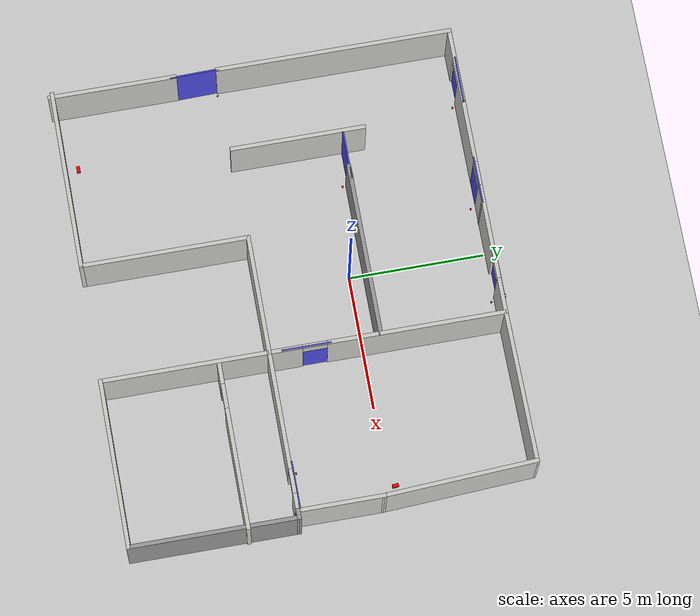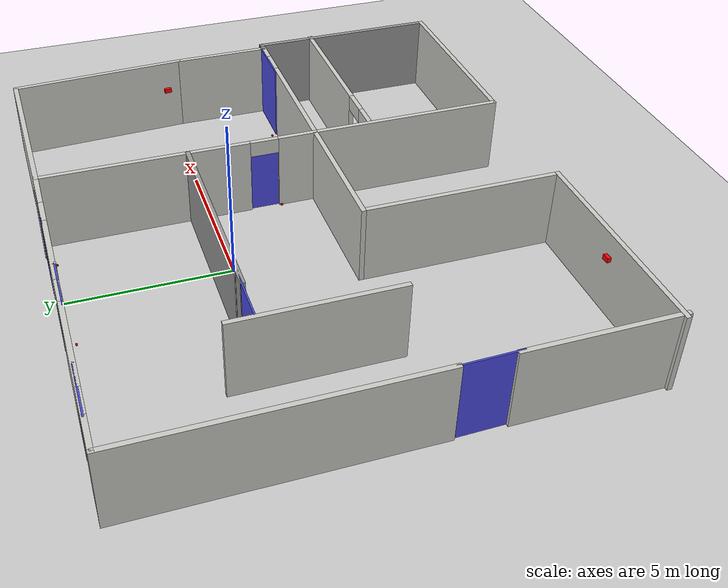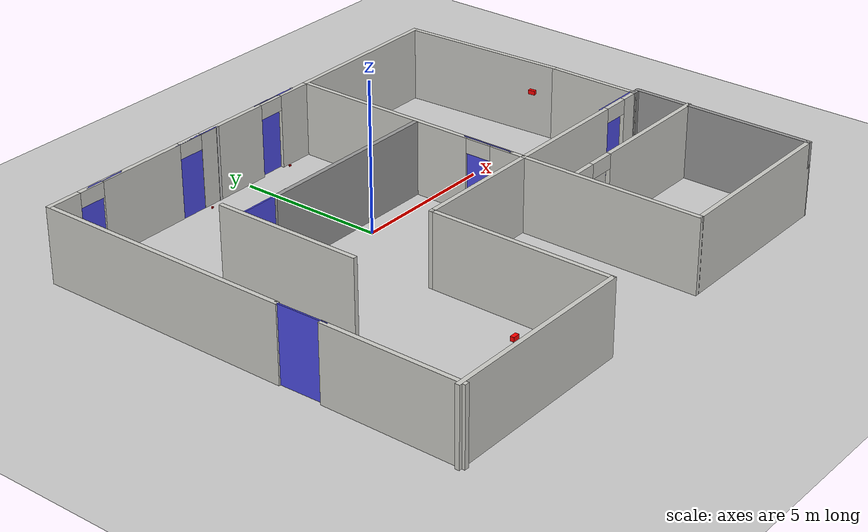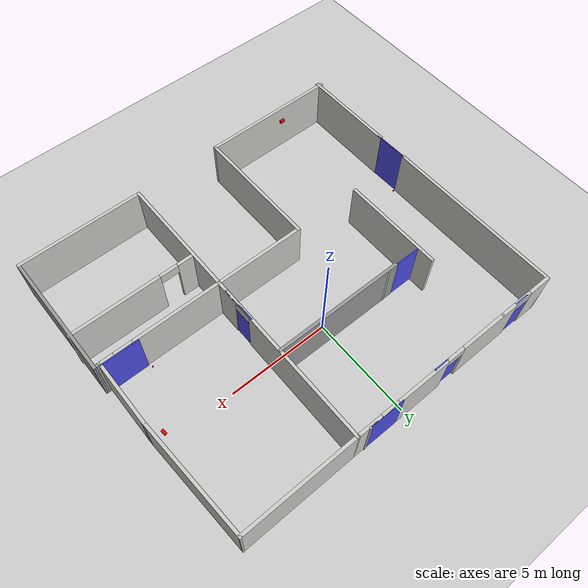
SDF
<sdf version="1.7">
 <world name="default">
  <light name="sun" type="directional">
   <pose>0 0 10 0 -0 0</pose>
   <diffuse>0.8 0.8 0.8 1</diffuse>
   <specular>0.2 0.2 0.2 1</specular>
   <attenuation>
    <range>1000</range>
    <constant>0.9</constant>
    <linear>0.01</linear>
    <quadratic>0.001</quadratic>
   </attenuation>
   <direction>-0.5 0.1 -0.9</direction>
   <spot><inner_angle>0</inner_angle><outer_angle>0</outer_angle><falloff>0</falloff></spot>
  </light>
  <model name="ground_plane">
   <static>1</static>
   <link name="link">
    <collision name="collision">
     <geometry><plane><normal>0 0 1</normal><size>100 100</size></plane></geometry>
     <surface><friction><ode><mu>100</mu><mu2>50</mu2></ode></friction></surface>
    </collision>
    <visual name="visual">
     <cast_shadows>0</cast_shadows>
     <geometry><plane><normal>0 0 1</normal><size>100 100</size></plane></geometry>
     <material>
      <script><uri>file://media/materials/scripts/gazebo.material</uri><name>Gazebo/Grey</name></script>
     </material>
    </visual>
   </link>
  </model>
  <gravity>0 0 -9.8</gravity>
  <magnetic_field>6e-06 2.3e-05 -4.2e-05</magnetic_field>
  <atmosphere type="adiabatic"/>
  <physics type="ode">
   <max_step_size>0.001</max_step_size>
   <real_time_factor>1</real_time_factor>
   <real_time_update_rate>1000</real_time_update_rate>
  </physics>
  <scene><ambient>0.4 0.4 0.4 1</ambient><background>0.7 0.7 0.7 1</background><shadows>1</shadows></scene>
  <spherical_coordinates>
   <surface_model>EARTH_WGS84</surface_model>
   <latitude_deg>0</latitude_deg>
   <longitude_deg>0</longitude_deg>
   <elevation>0</elevation>
   <heading_deg>0</heading_deg>
  </spherical_coordinates>
  <model name="simworld12">
   <link name="Wall_11">
    <pose>4.02518 1.54652 0 0 0 -1.5708</pose>
    <visual name="Wall_11_Visual_0">
     <pose>-1.09189 0 1.25 0 -0 0</pose>
     <geometry><box><size>6.56622 0.15 2.5</size></box></geometry>
     <material>
      <script><uri>file://media/materials/scripts/gazebo.material</uri><name>Gazebo/CeilingTiled</name></script>
      <ambient>1 1 1 1</ambient>
      <shader type="pixel"/>
     </material>
     <meta><layer>0</layer></meta>
    </visual>
    <visual name="Wall_11_Visual_1">
     <pose>3.73311 0 1.25 0 -0 0</pose>
     <geometry><box><size>1.28378 0.15 2.5</size></box></geometry>
     <material>
      <script><uri>file://media/materials/scripts/gazebo.material</uri><name>Gazebo/CeilingTiled</name></script>
      <ambient>1 1 1 1</ambient>
      <shader type="pixel"/>
     </material>
     <meta><layer>0</layer></meta>
    </visual>
    <visual name="Wall_11_Visual_2">
     <pose>2.64122 0 2.25 0 -0 0</pose>
     <geometry><box><size>0.9 0.15 0.5</size></box></geometry>
     <material>
      <script><uri>file://media/materials/scripts/gazebo.material</uri><name>Gazebo/CeilingTiled</name></script>
      <ambient>1 1 1 1</ambient>
      <shader type="pixel"/>
     </material>
     <meta><layer>0</layer></meta>
    </visual>
    <collision name="Wall_11_Collision_0">
     <pose>-1.09189 0 1.25 0 -0 0</pose>
     <geometry><box><size>6.56622 0.15 2.5</size></box></geometry>
     <surface>
      <friction>
       <ode><mu>1</mu><mu2>1</mu2><fdir1>0 0 0</fdir1><slip1>0</slip1><slip2>0</slip2></ode>
       <torsional>
        <coefficient>1</coefficient>
        <patch_radius>0</patch_radius>
        <surface_radius>0</surface_radius>
        <use_patch_radius>1</use_patch_radius>
        <ode><slip>0</slip></ode>
       </torsional>
      </friction>
      <bounce><restitution_coefficient>0</restitution_coefficient><threshold>1e+06</threshold></bounce>
      <contact>
       <collide_without_contact>0</collide_without_contact>
       <collide_without_contact_bitmask>1</collide_without_contact_bitmask>
       <collide_bitmask>1</collide_bitmask>
       <ode>
        <soft_cfm>0</soft_cfm>
        <soft_erp>0.2</soft_erp>
        <kp>1e+13</kp>
        <kd>1</kd>
        <max_vel>0.01</max_vel>
        <min_depth>0</min_depth>
       </ode>
       <bullet>
        <split_impulse>1</split_impulse>
        <split_impulse_penetration_threshold>-0.01</split_impulse_penetration_threshold>
        <soft_cfm>0</soft_cfm>
        <soft_erp>0.2</soft_erp>
        <kp>1e+13</kp>
        <kd>1</kd>
       </bullet>
      </contact>
     </surface>
    </collision>
    <collision name="Wall_11_Collision_1">
     <pose>3.73311 0 1.25 0 -0 0</pose>
     <geometry><box><size>1.28378 0.15 2.5</size></box></geometry>
     <surface>
      <friction>
       <ode><mu>1</mu><mu2>1</mu2><fdir1>0 0 0</fdir1><slip1>0</slip1><slip2>0</slip2></ode>
       <torsional>
        <coefficient>1</coefficient>
        <patch_radius>0</patch_radius>
        <surface_radius>0</surface_radius>
        <use_patch_radius>1</use_patch_radius>
        <ode><slip>0</slip></ode>
       </torsional>
      </friction>
      <bounce><restitution_coefficient>0</restitution_coefficient><threshold>1e+06</threshold></bounce>
      <contact>
       <collide_without_contact>0</collide_without_contact>
       <collide_without_contact_bitmask>1</collide_without_contact_bitmask>
       <collide_bitmask>1</collide_bitmask>
       <ode>
        <soft_cfm>0</soft_cfm>
        <soft_erp>0.2</soft_erp>
        <kp>1e+13</kp>
        <kd>1</kd>
        <max_vel>0.01</max_vel>
        <min_depth>0</min_depth>
       </ode>
       <bullet>
        <split_impulse>1</split_impulse>
        <split_impulse_penetration_threshold>-0.01</split_impulse_penetration_threshold>
        <soft_cfm>0</soft_cfm>
        <soft_erp>0.2</soft_erp>
        <kp>1e+13</kp>
        <kd>1</kd>
       </bullet>
      </contact>
     </surface>
    </collision>
    <collision name="Wall_11_Collision_2">
     <pose>2.64122 0 2.25 0 -0 0</pose>
     <geometry><box><size>0.9 0.15 0.5</size></box></geometry>
     <surface>
      <friction>
       <ode><mu>1</mu><mu2>1</mu2><fdir1>0 0 0</fdir1><slip1>0</slip1><slip2>0</slip2></ode>
       <torsional>
        <coefficient>1</coefficient>
        <patch_radius>0</patch_radius>
        <surface_radius>0</surface_radius>
        <use_patch_radius>1</use_patch_radius>
        <ode><slip>0</slip></ode>
       </torsional>
      </friction>
      <bounce><restitution_coefficient>0</restitution_coefficient><threshold>1e+06</threshold></bounce>
      <contact>
       <collide_without_contact>0</collide_without_contact>
       <collide_without_contact_bitmask>1</collide_without_contact_bitmask>
       <collide_bitmask>1</collide_bitmask>
       <ode>
        <soft_cfm>0</soft_cfm>
        <soft_erp>0.2</soft_erp>
        <kp>1e+13</kp>
        <kd>1</kd>
        <max_vel>0.01</max_vel>
        <min_depth>0</min_depth>
       </ode>
       <bullet>
        <split_impulse>1</split_impulse>
        <split_impulse_penetration_threshold>-0.01</split_impulse_penetration_threshold>
        <soft_cfm>0</soft_cfm>
        <soft_erp>0.2</soft_erp>
        <kp>1e+13</kp>
        <kd>1</kd>
       </bullet>
      </contact>
     </surface>
    </collision>
   </link>
   <link name="Wall_13">
    <pose>1.85018 -2.75348 0 0 -0 3.14159</pose>
    <visual name="Wall_13_Visual">
     <pose>0 0 1.25 0 -0 0</pose>
     <geometry><box><size>4.5 0.15 2.5</size></box></geometry>
     <material>
      <script><uri>file://media/materials/scripts/gazebo.material</uri><name>Gazebo/CeilingTiled</name></script>
      <ambient>1 1 1 1</ambient>
      <shader type="pixel"/>
     </material>
     <meta><layer>0</layer></meta>
    </visual>
    <collision name="Wall_13_Collision">
     <pose>0 0 1.25 0 -0 0</pose>
     <geometry><box><size>4.5 0.15 2.5</size></box></geometry>
     <surface>
      <friction>
       <ode><mu>1</mu><mu2>1</mu2><fdir1>0 0 0</fdir1><slip1>0</slip1><slip2>0</slip2></ode>
       <torsional>
        <coefficient>1</coefficient>
        <patch_radius>0</patch_radius>
        <surface_radius>0</surface_radius>
        <use_patch_radius>1</use_patch_radius>
        <ode><slip>0</slip></ode>
       </torsional>
      </friction>
      <bounce><restitution_coefficient>0</restitution_coefficient><threshold>1e+06</threshold></bounce>
      <contact>
       <collide_without_contact>0</collide_without_contact>
       <collide_without_contact_bitmask>1</collide_without_contact_bitmask>
       <collide_bitmask>1</collide_bitmask>
       <ode>
        <soft_cfm>0</soft_cfm>
        <soft_erp>0.2</soft_erp>
        <kp>1e+13</kp>
        <kd>1</kd>
        <max_vel>0.01</max_vel>
        <min_depth>0</min_depth>
       </ode>
       <bullet>
        <split_impulse>1</split_impulse>
        <split_impulse_penetration_threshold>-0.01</split_impulse_penetration_threshold>
        <soft_cfm>0</soft_cfm>
        <soft_erp>0.2</soft_erp>
        <kp>1e+13</kp>
        <kd>1</kd>
       </bullet>
      </contact>
     </surface>
    </collision>
   </link>
   <link name="Wall_14">
    <pose>-0.324822 -5.80348 0 0 0 -1.5708</pose>
    <visual name="Wall_14_Visual">
     <pose>0 0 1.25 0 -0 0</pose>
     <geometry><box><size>6.25 0.15 2.5</size></box></geometry>
     <material>
      <script><uri>file://media/materials/scripts/gazebo.material</uri><name>Gazebo/CeilingTiled</name></script>
      <ambient>1 1 1 1</ambient>
      <shader type="pixel"/>
     </material>
     <meta><layer>0</layer></meta>
    </visual>
    <collision name="Wall_14_Collision">
     <pose>0 0 1.25 0 -0 0</pose>
     <geometry><box><size>6.25 0.15 2.5</size></box></geometry>
     <surface>
      <friction>
       <ode><mu>1</mu><mu2>1</mu2><fdir1>0 0 0</fdir1><slip1>0</slip1><slip2>0</slip2></ode>
       <torsional>
        <coefficient>1</coefficient>
        <patch_radius>0</patch_radius>
        <surface_radius>0</surface_radius>
        <use_patch_radius>1</use_patch_radius>
        <ode><slip>0</slip></ode>
       </torsional>
      </friction>
      <bounce><restitution_coefficient>0</restitution_coefficient><threshold>1e+06</threshold></bounce>
      <contact>
       <collide_without_contact>0</collide_without_contact>
       <collide_without_contact_bitmask>1</collide_without_contact_bitmask>
       <collide_bitmask>1</collide_bitmask>
       <ode>
        <soft_cfm>0</soft_cfm>
        <soft_erp>0.2</soft_erp>
        <kp>1e+13</kp>
        <kd>1</kd>
        <max_vel>0.01</max_vel>
        <min_depth>0</min_depth>
       </ode>
       <bullet>
        <split_impulse>1</split_impulse>
        <split_impulse_penetration_threshold>-0.01</split_impulse_penetration_threshold>
        <soft_cfm>0</soft_cfm>
        <soft_erp>0.2</soft_erp>
        <kp>1e+13</kp>
        <kd>1</kd>
       </bullet>
      </contact>
     </surface>
    </collision>
   </link>
   <link name="Wall_15">
    <pose>-3.62482 -8.85348 0 0 -0 3.14159</pose>
    <visual name="Wall_15_Visual">
     <pose>0 0 1.25 0 -0 0</pose>
     <geometry><box><size>6.75 0.15 2.5</size></box></geometry>
     <material>
      <script><uri>file://media/materials/scripts/gazebo.material</uri><name>Gazebo/CeilingTiled</name></script>
      <ambient>1 1 1 1</ambient>
      <shader type="pixel"/>
     </material>
     <meta><layer>0</layer></meta>
    </visual>
    <collision name="Wall_15_Collision">
     <pose>0 0 1.25 0 -0 0</pose>
     <geometry><box><size>6.75 0.15 2.5</size></box></geometry>
     <surface>
      <friction>
       <ode><mu>1</mu><mu2>1</mu2><fdir1>0 0 0</fdir1><slip1>0</slip1><slip2>0</slip2></ode>
       <torsional>
        <coefficient>1</coefficient>
        <patch_radius>0</patch_radius>
        <surface_radius>0</surface_radius>
        <use_patch_radius>1</use_patch_radius>
        <ode><slip>0</slip></ode>
       </torsional>
      </friction>
      <bounce><restitution_coefficient>0</restitution_coefficient><threshold>1e+06</threshold></bounce>
      <contact>
       <collide_without_contact>0</collide_without_contact>
       <collide_without_contact_bitmask>1</collide_without_contact_bitmask>
       <collide_bitmask>1</collide_bitmask>
       <ode>
        <soft_cfm>0</soft_cfm>
        <soft_erp>0.2</soft_erp>
        <kp>1e+13</kp>
        <kd>1</kd>
        <max_vel>0.01</max_vel>
        <min_depth>0</min_depth>
       </ode>
       <bullet>
        <split_impulse>1</split_impulse>
        <split_impulse_penetration_threshold>-0.01</split_impulse_penetration_threshold>
        <soft_cfm>0</soft_cfm>
        <soft_erp>0.2</soft_erp>
        <kp>1e+13</kp>
        <kd>1</kd>
       </bullet>
      </contact>
     </surface>
    </collision>
   </link>
   <link name="Wall_18">
    <pose>-3.72482 -0.32848 0 0 -0 1.5708</pose>
    <visual name="Wall_18_Visual">
     <pose>0 0 1.25 0 -0 0</pose>
     <geometry><box><size>5 0.15 2.5</size></box></geometry>
     <material>
      <script><uri>file://media/materials/scripts/gazebo.material</uri><name>Gazebo/CeilingTiled</name></script>
      <ambient>1 1 1 1</ambient>
      <shader type="pixel"/>
     </material>
     <meta><layer>0</layer></meta>
    </visual>
    <collision name="Wall_18_Collision">
     <pose>0 0 1.25 0 -0 0</pose>
     <geometry><box><size>5 0.15 2.5</size></box></geometry>
     <surface>
      <friction>
       <ode><mu>1</mu><mu2>1</mu2><fdir1>0 0 0</fdir1><slip1>0</slip1><slip2>0</slip2></ode>
       <torsional>
        <coefficient>1</coefficient>
        <patch_radius>0</patch_radius>
        <surface_radius>0</surface_radius>
        <use_patch_radius>1</use_patch_radius>
        <ode><slip>0</slip></ode>
       </torsional>
      </friction>
      <bounce><restitution_coefficient>0</restitution_coefficient><threshold>1e+06</threshold></bounce>
      <contact>
       <collide_without_contact>0</collide_without_contact>
       <collide_without_contact_bitmask>1</collide_without_contact_bitmask>
       <collide_bitmask>1</collide_bitmask>
       <ode>
        <soft_cfm>0</soft_cfm>
        <soft_erp>0.2</soft_erp>
        <kp>1e+13</kp>
        <kd>1</kd>
        <max_vel>0.01</max_vel>
        <min_depth>0</min_depth>
       </ode>
       <bullet>
        <split_impulse>1</split_impulse>
        <split_impulse_penetration_threshold>-0.01</split_impulse_penetration_threshold>
        <soft_cfm>0</soft_cfm>
        <soft_erp>0.2</soft_erp>
        <kp>1e+13</kp>
        <kd>1</kd>
       </bullet>
      </contact>
     </surface>
    </collision>
   </link>
   <link name="Wall_21">
    <pose>0.835818 1.29652 0 0 -0 0</pose>
    <visual name="Wall_21_Visual">
     <pose>0 0 1.25 0 -0 0</pose>
     <geometry><box><size>6.5 0.15 2.5</size></box></geometry>
     <material>
      <script><uri>file://media/materials/scripts/gazebo.material</uri><name>Gazebo/Grey</name></script>
      <ambient>1 1 1 1</ambient>
      <shader type="pixel"/>
     </material>
     <meta><layer>0</layer></meta>
    </visual>
    <collision name="Wall_21_Collision">
     <pose>0 0 1.25 0 -0 0</pose>
     <geometry><box><size>6.5 0.15 2.5</size></box></geometry>
     <surface>
      <friction>
       <ode><mu>1</mu><mu2>1</mu2><fdir1>0 0 0</fdir1><slip1>0</slip1><slip2>0</slip2></ode>
       <torsional>
        <coefficient>1</coefficient>
        <patch_radius>0</patch_radius>
        <surface_radius>0</surface_radius>
        <use_patch_radius>1</use_patch_radius>
        <ode><slip>0</slip></ode>
       </torsional>
      </friction>
      <bounce><restitution_coefficient>0</restitution_coefficient><threshold>1e+06</threshold></bounce>
      <contact>
       <collide_without_contact>0</collide_without_contact>
       <collide_without_contact_bitmask>1</collide_without_contact_bitmask>
       <collide_bitmask>1</collide_bitmask>
       <ode>
        <soft_cfm>0</soft_cfm>
        <soft_erp>0.2</soft_erp>
        <kp>1e+13</kp>
        <kd>1</kd>
        <max_vel>0.01</max_vel>
        <min_depth>0</min_depth>
       </ode>
       <bullet>
        <split_impulse>1</split_impulse>
        <split_impulse_penetration_threshold>-0.01</split_impulse_penetration_threshold>
        <soft_cfm>0</soft_cfm>
        <soft_erp>0.2</soft_erp>
        <kp>1e+13</kp>
        <kd>1</kd>
       </bullet>
      </contact>
     </surface>
    </collision>
   </link>
   <link name="Wall_24">
    <pose>9.87294 -1.20609 0 0 0 -1.5708</pose>
    <visual name="Wall_24_Visual">
     <pose>0 0 1.25 0 -0 0</pose>
     <geometry><box><size>3.25 0.15 2.5</size></box></geometry>
     <material>
      <script><uri>file://media/materials/scripts/gazebo.material</uri><name>Gazebo/CeilingTiled</name></script>
      <ambient>1 1 1 1</ambient>
      <shader type="pixel"/>
     </material>
     <meta><layer>0</layer></meta>
    </visual>
    <collision name="Wall_24_Collision">
     <pose>0 0 1.25 0 -0 0</pose>
     <geometry><box><size>3.25 0.15 2.5</size></box></geometry>
     <surface>
      <friction>
       <ode><mu>1</mu><mu2>1</mu2><fdir1>0 0 0</fdir1><slip1>0</slip1><slip2>0</slip2></ode>
       <torsional>
        <coefficient>1</coefficient>
        <patch_radius>0</patch_radius>
        <surface_radius>0</surface_radius>
        <use_patch_radius>1</use_patch_radius>
        <ode><slip>0</slip></ode>
       </torsional>
      </friction>
      <bounce><restitution_coefficient>0</restitution_coefficient><threshold>1e+06</threshold></bounce>
      <contact>
       <collide_without_contact>0</collide_without_contact>
       <collide_without_contact_bitmask>1</collide_without_contact_bitmask>
       <collide_bitmask>1</collide_bitmask>
       <ode>
        <soft_cfm>0</soft_cfm>
        <soft_erp>0.2</soft_erp>
        <kp>1e+13</kp>
        <kd>1</kd>
        <max_vel>0.01</max_vel>
        <min_depth>0</min_depth>
       </ode>
       <bullet>
        <split_impulse>1</split_impulse>
        <split_impulse_penetration_threshold>-0.01</split_impulse_penetration_threshold>
        <soft_cfm>0</soft_cfm>
        <soft_erp>0.2</soft_erp>
        <kp>1e+13</kp>
        <kd>1</kd>
       </bullet>
      </contact>
     </surface>
    </collision>
   </link>
   <link name="Wall_25">
    <pose>6.94906 -2.75479 0 0 -0 3.14115</pose>
    <visual name="Wall_25_Visual_0">
     <pose>-2.64457 0 1.25 0 -0 0</pose>
     <geometry><box><size>0.708624 0.15 2.5</size></box></geometry>
     <material>
      <script><uri>file://media/materials/scripts/gazebo.material</uri><name>Gazebo/CeilingTiled</name></script>
      <ambient>1 1 1 1</ambient>
      <shader type="pixel"/>
     </material>
     <meta><layer>0</layer></meta>
    </visual>
    <visual name="Wall_25_Visual_1">
     <pose>0.804312 0 1.25 0 -0 0</pose>
     <geometry><box><size>4.38914 0.15 2.5</size></box></geometry>
     <material>
      <script><uri>file://media/materials/scripts/gazebo.material</uri><name>Gazebo/CeilingTiled</name></script>
      <ambient>1 1 1 1</ambient>
      <shader type="pixel"/>
     </material>
     <meta><layer>0</layer></meta>
    </visual>
    <visual name="Wall_25_Visual_2">
     <pose>-1.84026 0 2.25 0 -0 0</pose>
     <geometry><box><size>0.9 0.15 0.5</size></box></geometry>
     <material>
      <script><uri>file://media/materials/scripts/gazebo.material</uri><name>Gazebo/CeilingTiled</name></script>
      <ambient>1 1 1 1</ambient>
      <shader type="pixel"/>
     </material>
     <meta><layer>0</layer></meta>
    </visual>
    <collision name="Wall_25_Collision_0">
     <pose>-2.64457 0 1.25 0 -0 0</pose>
     <geometry><box><size>0.708624 0.15 2.5</size></box></geometry>
     <surface>
      <friction>
       <ode><mu>1</mu><mu2>1</mu2><fdir1>0 0 0</fdir1><slip1>0</slip1><slip2>0</slip2></ode>
       <torsional>
        <coefficient>1</coefficient>
        <patch_radius>0</patch_radius>
        <surface_radius>0</surface_radius>
        <use_patch_radius>1</use_patch_radius>
        <ode><slip>0</slip></ode>
       </torsional>
      </friction>
      <bounce><restitution_coefficient>0</restitution_coefficient><threshold>1e+06</threshold></bounce>
      <contact>
       <collide_without_contact>0</collide_without_contact>
       <collide_without_contact_bitmask>1</collide_without_contact_bitmask>
       <collide_bitmask>1</collide_bitmask>
       <ode>
        <soft_cfm>0</soft_cfm>
        <soft_erp>0.2</soft_erp>
        <kp>1e+13</kp>
        <kd>1</kd>
        <max_vel>0.01</max_vel>
        <min_depth>0</min_depth>
       </ode>
       <bullet>
        <split_impulse>1</split_impulse>
        <split_impulse_penetration_threshold>-0.01</split_impulse_penetration_threshold>
        <soft_cfm>0</soft_cfm>
        <soft_erp>0.2</soft_erp>
        <kp>1e+13</kp>
        <kd>1</kd>
       </bullet>
      </contact>
     </surface>
    </collision>
    <collision name="Wall_25_Collision_1">
     <pose>0.804312 0 1.25 0 -0 0</pose>
     <geometry><box><size>4.38914 0.15 2.5</size></box></geometry>
     <surface>
      <friction>
       <ode><mu>1</mu><mu2>1</mu2><fdir1>0 0 0</fdir1><slip1>0</slip1><slip2>0</slip2></ode>
       <torsional>
        <coefficient>1</coefficient>
        <patch_radius>0</patch_radius>
        <surface_radius>0</surface_radius>
        <use_patch_radius>1</use_patch_radius>
        <ode><slip>0</slip></ode>
       </torsional>
      </friction>
      <bounce><restitution_coefficient>0</restitution_coefficient><threshold>1e+06</threshold></bounce>
      <contact>
       <collide_without_contact>0</collide_without_contact>
       <collide_without_contact_bitmask>1</collide_without_contact_bitmask>
       <collide_bitmask>1</collide_bitmask>
       <ode>
        <soft_cfm>0</soft_cfm>
        <soft_erp>0.2</soft_erp>
        <kp>1e+13</kp>
        <kd>1</kd>
        <max_vel>0.01</max_vel>
        <min_depth>0</min_depth>
       </ode>
       <bullet>
        <split_impulse>1</split_impulse>
        <split_impulse_penetration_threshold>-0.01</split_impulse_penetration_threshold>
        <soft_cfm>0</soft_cfm>
        <soft_erp>0.2</soft_erp>
        <kp>1e+13</kp>
        <kd>1</kd>
       </bullet>
      </contact>
     </surface>
    </collision>
    <collision name="Wall_25_Collision_2">
     <pose>-1.84026 0 2.25 0 -0 0</pose>
     <geometry><box><size>0.9 0.15 0.5</size></box></geometry>
     <surface>
      <friction>
       <ode><mu>1</mu><mu2>1</mu2><fdir1>0 0 0</fdir1><slip1>0</slip1><slip2>0</slip2></ode>
       <torsional>
        <coefficient>1</coefficient>
        <patch_radius>0</patch_radius>
        <surface_radius>0</surface_radius>
        <use_patch_radius>1</use_patch_radius>
        <ode><slip>0</slip></ode>
       </torsional>
      </friction>
      <bounce><restitution_coefficient>0</restitution_coefficient><threshold>1e+06</threshold></bounce>
      <contact>
       <collide_without_contact>0</collide_without_contact>
       <collide_without_contact_bitmask>1</collide_without_contact_bitmask>
       <collide_bitmask>1</collide_bitmask>
       <ode>
        <soft_cfm>0</soft_cfm>
        <soft_erp>0.2</soft_erp>
        <kp>1e+13</kp>
        <kd>1</kd>
        <max_vel>0.01</max_vel>
        <min_depth>0</min_depth>
       </ode>
       <bullet>
        <split_impulse>1</split_impulse>
        <split_impulse_penetration_threshold>-0.01</split_impulse_penetration_threshold>
        <soft_cfm>0</soft_cfm>
        <soft_erp>0.2</soft_erp>
        <kp>1e+13</kp>
        <kd>1</kd>
       </bullet>
      </contact>
     </surface>
    </collision>
   </link>
   <link name="Wall_26">
    <pose>4.02518 -5.80348 0 0 0 -1.5708</pose>
    <visual name="Wall_26_Visual">
     <pose>0 0 1.25 0 -0 0</pose>
     <geometry><box><size>6.25 0.15 2.5</size></box></geometry>
     <material>
      <script><uri>file://media/materials/scripts/gazebo.material</uri><name>Gazebo/CeilingTiled</name></script>
      <ambient>1 1 1 1</ambient>
      <shader type="pixel"/>
     </material>
     <meta><layer>0</layer></meta>
    </visual>
    <collision name="Wall_26_Collision">
     <pose>0 0 1.25 0 -0 0</pose>
     <geometry><box><size>6.25 0.15 2.5</size></box></geometry>
     <surface>
      <friction>
       <ode><mu>1</mu><mu2>1</mu2><fdir1>0 0 0</fdir1><slip1>0</slip1><slip2>0</slip2></ode>
       <torsional>
        <coefficient>1</coefficient>
        <patch_radius>0</patch_radius>
        <surface_radius>0</surface_radius>
        <use_patch_radius>1</use_patch_radius>
        <ode><slip>0</slip></ode>
       </torsional>
      </friction>
      <bounce><restitution_coefficient>0</restitution_coefficient><threshold>1e+06</threshold></bounce>
      <contact>
       <collide_without_contact>0</collide_without_contact>
       <collide_without_contact_bitmask>1</collide_without_contact_bitmask>
       <collide_bitmask>1</collide_bitmask>
       <ode>
        <soft_cfm>0</soft_cfm>
        <soft_erp>0.2</soft_erp>
        <kp>1e+13</kp>
        <kd>1</kd>
        <max_vel>0.01</max_vel>
        <min_depth>0</min_depth>
       </ode>
       <bullet>
        <split_impulse>1</split_impulse>
        <split_impulse_penetration_threshold>-0.01</split_impulse_penetration_threshold>
        <soft_cfm>0</soft_cfm>
        <soft_erp>0.2</soft_erp>
        <kp>1e+13</kp>
        <kd>1</kd>
       </bullet>
      </contact>
     </surface>
    </collision>
   </link>
   <link name="Wall_27">
    <pose>7.07518 -8.85348 0 0 -0 0</pose>
    <visual name="Wall_27_Visual">
     <pose>0 0 1.25 0 -0 0</pose>
     <geometry><box><size>6.25 0.15 2.5</size></box></geometry>
     <material>
      <script><uri>file://media/materials/scripts/gazebo.material</uri><name>Gazebo/CeilingTiled</name></script>
      <ambient>1 1 1 1</ambient>
      <shader type="pixel"/>
     </material>
     <meta><layer>0</layer></meta>
    </visual>
    <collision name="Wall_27_Collision">
     <pose>0 0 1.25 0 -0 0</pose>
     <geometry><box><size>6.25 0.15 2.5</size></box></geometry>
     <surface>
      <friction>
       <ode><mu>1</mu><mu2>1</mu2><fdir1>0 0 0</fdir1><slip1>0</slip1><slip2>0</slip2></ode>
       <torsional>
        <coefficient>1</coefficient>
        <patch_radius>0</patch_radius>
        <surface_radius>0</surface_radius>
        <use_patch_radius>1</use_patch_radius>
        <ode><slip>0</slip></ode>
       </torsional>
      </friction>
      <bounce><restitution_coefficient>0</restitution_coefficient><threshold>1e+06</threshold></bounce>
      <contact>
       <collide_without_contact>0</collide_without_contact>
       <collide_without_contact_bitmask>1</collide_without_contact_bitmask>
       <collide_bitmask>1</collide_bitmask>
       <ode>
        <soft_cfm>0</soft_cfm>
        <soft_erp>0.2</soft_erp>
        <kp>1e+13</kp>
        <kd>1</kd>
        <max_vel>0.01</max_vel>
        <min_depth>0</min_depth>
       </ode>
       <bullet>
        <split_impulse>1</split_impulse>
        <split_impulse_penetration_threshold>-0.01</split_impulse_penetration_threshold>
        <soft_cfm>0</soft_cfm>
        <soft_erp>0.2</soft_erp>
        <kp>1e+13</kp>
        <kd>1</kd>
       </bullet>
      </contact>
     </surface>
    </collision>
   </link>
   <link name="Wall_28">
    <pose>10.1252 -5.80348 0 0 -0 1.5708</pose>
    <visual name="Wall_28_Visual">
     <pose>0 0 1.25 0 -0 0</pose>
     <geometry><box><size>6.25 0.15 2.5</size></box></geometry>
     <material>
      <script><uri>file://media/materials/scripts/gazebo.material</uri><name>Gazebo/Grey</name></script>
      <ambient>1 1 1 1</ambient>
      <shader type="pixel"/>
     </material>
     <meta><layer>0</layer></meta>
    </visual>
    <collision name="Wall_28_Collision">
     <pose>0 0 1.25 0 -0 0</pose>
     <geometry><box><size>6.25 0.15 2.5</size></box></geometry>
     <surface>
      <friction>
       <ode><mu>1</mu><mu2>1</mu2><fdir1>0 0 0</fdir1><slip1>0</slip1><slip2>0</slip2></ode>
       <torsional>
        <coefficient>1</coefficient>
        <patch_radius>0</patch_radius>
        <surface_radius>0</surface_radius>
        <use_patch_radius>1</use_patch_radius>
        <ode><slip>0</slip></ode>
       </torsional>
      </friction>
      <bounce><restitution_coefficient>0</restitution_coefficient><threshold>1e+06</threshold></bounce>
      <contact>
       <collide_without_contact>0</collide_without_contact>
       <collide_without_contact_bitmask>1</collide_without_contact_bitmask>
       <collide_bitmask>1</collide_bitmask>
       <ode>
        <soft_cfm>0</soft_cfm>
        <soft_erp>0.2</soft_erp>
        <kp>1e+13</kp>
        <kd>1</kd>
        <max_vel>0.01</max_vel>
        <min_depth>0</min_depth>
       </ode>
       <bullet>
        <split_impulse>1</split_impulse>
        <split_impulse_penetration_threshold>-0.01</split_impulse_penetration_threshold>
        <soft_cfm>0</soft_cfm>
        <soft_erp>0.2</soft_erp>
        <kp>1e+13</kp>
        <kd>1</kd>
       </bullet>
      </contact>
     </surface>
    </collision>
   </link>
   <link name="Wall_29">
    <pose>9.99906 -2.75479 0 0 0 -3.13125</pose>
    <visual name="Wall_29_Visual">
     <pose>0 0 1.25 0 -0 0</pose>
     <geometry><box><size>0.402248 0.15 2.5</size></box></geometry>
     <material>
      <script><uri>file://media/materials/scripts/gazebo.material</uri><name>Gazebo/Grey</name></script>
      <ambient>1 1 1 1</ambient>
      <shader type="pixel"/>
     </material>
     <meta><layer>0</layer></meta>
    </visual>
    <collision name="Wall_29_Collision">
     <pose>0 0 1.25 0 -0 0</pose>
     <geometry><box><size>0.402248 0.15 2.5</size></box></geometry>
     <surface>
      <friction>
       <ode><mu>1</mu><mu2>1</mu2><fdir1>0 0 0</fdir1><slip1>0</slip1><slip2>0</slip2></ode>
       <torsional>
        <coefficient>1</coefficient>
        <patch_radius>0</patch_radius>
        <surface_radius>0</surface_radius>
        <use_patch_radius>1</use_patch_radius>
        <ode><slip>0</slip></ode>
       </torsional>
      </friction>
      <bounce><restitution_coefficient>0</restitution_coefficient><threshold>1e+06</threshold></bounce>
      <contact>
       <collide_without_contact>0</collide_without_contact>
       <collide_without_contact_bitmask>1</collide_without_contact_bitmask>
       <collide_bitmask>1</collide_bitmask>
       <ode>
        <soft_cfm>0</soft_cfm>
        <soft_erp>0.2</soft_erp>
        <kp>1e+13</kp>
        <kd>1</kd>
        <max_vel>0.01</max_vel>
        <min_depth>0</min_depth>
       </ode>
       <bullet>
        <split_impulse>1</split_impulse>
        <split_impulse_penetration_threshold>-0.01</split_impulse_penetration_threshold>
        <soft_cfm>0</soft_cfm>
        <soft_erp>0.2</soft_erp>
        <kp>1e+13</kp>
        <kd>1</kd>
       </bullet>
      </contact>
     </surface>
    </collision>
   </link>
   <link name="Wall_3">
    <pose>-6.82482 -6.65348 0 0 -0 1.5708</pose>
    <visual name="Wall_3_Visual">
     <pose>0 0 1.25 0 -0 0</pose>
     <geometry><box><size>4.75 0.15 2.5</size></box></geometry>
     <material>
      <script><uri>file://media/materials/scripts/gazebo.material</uri><name>Gazebo/CeilingTiled</name></script>
      <ambient>1 1 1 1</ambient>
      <shader type="pixel"/>
     </material>
     <meta><layer>0</layer></meta>
    </visual>
    <collision name="Wall_3_Collision">
     <pose>0 0 1.25 0 -0 0</pose>
     <geometry><box><size>4.75 0.15 2.5</size></box></geometry>
     <surface>
      <friction>
       <ode><mu>1</mu><mu2>1</mu2><fdir1>0 0 0</fdir1><slip1>0</slip1><slip2>0</slip2></ode>
       <torsional>
        <coefficient>1</coefficient>
        <patch_radius>0</patch_radius>
        <surface_radius>0</surface_radius>
        <use_patch_radius>1</use_patch_radius>
        <ode><slip>0</slip></ode>
       </torsional>
      </friction>
      <bounce><restitution_coefficient>0</restitution_coefficient><threshold>1e+06</threshold></bounce>
      <contact>
       <collide_without_contact>0</collide_without_contact>
       <collide_without_contact_bitmask>1</collide_without_contact_bitmask>
       <collide_bitmask>1</collide_bitmask>
       <ode>
        <soft_cfm>0</soft_cfm>
        <soft_erp>0.2</soft_erp>
        <kp>1e+13</kp>
        <kd>1</kd>
        <max_vel>0.01</max_vel>
        <min_depth>0</min_depth>
       </ode>
       <bullet>
        <split_impulse>1</split_impulse>
        <split_impulse_penetration_threshold>-0.01</split_impulse_penetration_threshold>
        <soft_cfm>0</soft_cfm>
        <soft_erp>0.2</soft_erp>
        <kp>1e+13</kp>
        <kd>1</kd>
       </bullet>
      </contact>
     </surface>
    </collision>
   </link>
   <link name="Wall_33">
    <pose>7.12482 -4.58462 0 0 -0 0</pose>
    <visual name="Wall_33_Visual_0">
     <pose>-2.68766 0 1.25 0 -0 0</pose>
     <geometry><box><size>0.874678 0.15 2.5</size></box></geometry>
     <material>
      <script><uri>file://media/materials/scripts/gazebo.material</uri><name>Gazebo/CeilingTiled</name></script>
      <ambient>1 1 1 1</ambient>
      <shader type="pixel"/>
     </material>
     <meta><layer>0</layer></meta>
    </visual>
    <visual name="Wall_33_Visual_1">
     <pose>0.887339 0 1.25 0 -0 0</pose>
     <geometry><box><size>4.47532 0.15 2.5</size></box></geometry>
     <material>
      <script><uri>file://media/materials/scripts/gazebo.material</uri><name>Gazebo/CeilingTiled</name></script>
      <ambient>1 1 1 1</ambient>
      <shader type="pixel"/>
     </material>
     <meta><layer>0</layer></meta>
    </visual>
    <visual name="Wall_33_Visual_2">
     <pose>-1.80032 0 2.25 0 -0 0</pose>
     <geometry><box><size>0.9 0.15 0.5</size></box></geometry>
     <material>
      <script><uri>file://media/materials/scripts/gazebo.material</uri><name>Gazebo/CeilingTiled</name></script>
      <ambient>1 1 1 1</ambient>
      <shader type="pixel"/>
     </material>
     <meta><layer>0</layer></meta>
    </visual>
    <collision name="Wall_33_Collision_0">
     <pose>-2.68766 0 1.25 0 -0 0</pose>
     <geometry><box><size>0.874678 0.15 2.5</size></box></geometry>
     <surface>
      <friction>
       <ode><mu>1</mu><mu2>1</mu2><fdir1>0 0 0</fdir1><slip1>0</slip1><slip2>0</slip2></ode>
       <torsional>
        <coefficient>1</coefficient>
        <patch_radius>0</patch_radius>
        <surface_radius>0</surface_radius>
        <use_patch_radius>1</use_patch_radius>
        <ode><slip>0</slip></ode>
       </torsional>
      </friction>
      <bounce><restitution_coefficient>0</restitution_coefficient><threshold>1e+06</threshold></bounce>
      <contact>
       <collide_without_contact>0</collide_without_contact>
       <collide_without_contact_bitmask>1</collide_without_contact_bitmask>
       <collide_bitmask>1</collide_bitmask>
       <ode>
        <soft_cfm>0</soft_cfm>
        <soft_erp>0.2</soft_erp>
        <kp>1e+13</kp>
        <kd>1</kd>
        <max_vel>0.01</max_vel>
        <min_depth>0</min_depth>
       </ode>
       <bullet>
        <split_impulse>1</split_impulse>
        <split_impulse_penetration_threshold>-0.01</split_impulse_penetration_threshold>
        <soft_cfm>0</soft_cfm>
        <soft_erp>0.2</soft_erp>
        <kp>1e+13</kp>
        <kd>1</kd>
       </bullet>
      </contact>
     </surface>
    </collision>
    <collision name="Wall_33_Collision_1">
     <pose>0.887339 0 1.25 0 -0 0</pose>
     <geometry><box><size>4.47532 0.15 2.5</size></box></geometry>
     <surface>
      <friction>
       <ode><mu>1</mu><mu2>1</mu2><fdir1>0 0 0</fdir1><slip1>0</slip1><slip2>0</slip2></ode>
       <torsional>
        <coefficient>1</coefficient>
        <patch_radius>0</patch_radius>
        <surface_radius>0</surface_radius>
        <use_patch_radius>1</use_patch_radius>
        <ode><slip>0</slip></ode>
       </torsional>
      </friction>
      <bounce><restitution_coefficient>0</restitution_coefficient><threshold>1e+06</threshold></bounce>
      <contact>
       <collide_without_contact>0</collide_without_contact>
       <collide_without_contact_bitmask>1</collide_without_contact_bitmask>
       <collide_bitmask>1</collide_bitmask>
       <ode>
        <soft_cfm>0</soft_cfm>
        <soft_erp>0.2</soft_erp>
        <kp>1e+13</kp>
        <kd>1</kd>
        <max_vel>0.01</max_vel>
        <min_depth>0</min_depth>
       </ode>
       <bullet>
        <split_impulse>1</split_impulse>
        <split_impulse_penetration_threshold>-0.01</split_impulse_penetration_threshold>
        <soft_cfm>0</soft_cfm>
        <soft_erp>0.2</soft_erp>
        <kp>1e+13</kp>
        <kd>1</kd>
       </bullet>
      </contact>
     </surface>
    </collision>
    <collision name="Wall_33_Collision_2">
     <pose>-1.80032 0 2.25 0 -0 0</pose>
     <geometry><box><size>0.9 0.15 0.5</size></box></geometry>
     <surface>
      <friction>
       <ode><mu>1</mu><mu2>1</mu2><fdir1>0 0 0</fdir1><slip1>0</slip1><slip2>0</slip2></ode>
       <torsional>
        <coefficient>1</coefficient>
        <patch_radius>0</patch_radius>
        <surface_radius>0</surface_radius>
        <use_patch_radius>1</use_patch_radius>
        <ode><slip>0</slip></ode>
       </torsional>
      </friction>
      <bounce><restitution_coefficient>0</restitution_coefficient><threshold>1e+06</threshold></bounce>
      <contact>
       <collide_without_contact>0</collide_without_contact>
       <collide_without_contact_bitmask>1</collide_without_contact_bitmask>
       <collide_bitmask>1</collide_bitmask>
       <ode>
        <soft_cfm>0</soft_cfm>
        <soft_erp>0.2</soft_erp>
        <kp>1e+13</kp>
        <kd>1</kd>
        <max_vel>0.01</max_vel>
        <min_depth>0</min_depth>
       </ode>
       <bullet>
        <split_impulse>1</split_impulse>
        <split_impulse_penetration_threshold>-0.01</split_impulse_penetration_threshold>
        <soft_cfm>0</soft_cfm>
        <soft_erp>0.2</soft_erp>
        <kp>1e+13</kp>
        <kd>1</kd>
       </bullet>
      </contact>
     </surface>
    </collision>
   </link>
   <link name="Wall_36">
    <pose>6.79946 5.87061 0 0 0 -3.13291</pose>
    <visual name="Wall_36_Visual">
     <pose>0 0 1.25 0 -0 0</pose>
     <geometry><box><size>5.69876 0.15 2.5</size></box></geometry>
     <material>
      <script><uri>file://media/materials/scripts/gazebo.material</uri><name>Gazebo/CeilingTiled</name></script>
      <ambient>1 1 1 1</ambient>
      <shader type="pixel"/>
     </material>
     <meta><layer>0</layer></meta>
    </visual>
    <collision name="Wall_36_Collision">
     <pose>0 0 1.25 0 -0 0</pose>
     <geometry><box><size>5.69876 0.15 2.5</size></box></geometry>
     <surface>
      <friction>
       <ode><mu>1</mu><mu2>1</mu2><fdir1>0 0 0</fdir1><slip1>0</slip1><slip2>0</slip2></ode>
       <torsional>
        <coefficient>1</coefficient>
        <patch_radius>0</patch_radius>
        <surface_radius>0</surface_radius>
        <use_patch_radius>1</use_patch_radius>
        <ode><slip>0</slip></ode>
       </torsional>
      </friction>
      <bounce><restitution_coefficient>0</restitution_coefficient><threshold>1e+06</threshold></bounce>
      <contact>
       <collide_without_contact>0</collide_without_contact>
       <collide_without_contact_bitmask>1</collide_without_contact_bitmask>
       <collide_bitmask>1</collide_bitmask>
       <ode>
        <soft_cfm>0</soft_cfm>
        <soft_erp>0.2</soft_erp>
        <kp>1e+13</kp>
        <kd>1</kd>
        <max_vel>0.01</max_vel>
        <min_depth>0</min_depth>
       </ode>
       <bullet>
        <split_impulse>1</split_impulse>
        <split_impulse_penetration_threshold>-0.01</split_impulse_penetration_threshold>
        <soft_cfm>0</soft_cfm>
        <soft_erp>0.2</soft_erp>
        <kp>1e+13</kp>
        <kd>1</kd>
       </bullet>
      </contact>
     </surface>
    </collision>
   </link>
   <link name="Wall_38">
    <pose>9.72334 3.1193 0 0 0 -1.51694</pose>
    <visual name="Wall_38_Visual">
     <pose>0 0 1.25 0 -0 0</pose>
     <geometry><box><size>5.70885 0.15 2.5</size></box></geometry>
     <material>
      <script><uri>file://media/materials/scripts/gazebo.material</uri><name>Gazebo/CeilingTiled</name></script>
      <ambient>1 1 1 1</ambient>
      <shader type="pixel"/>
     </material>
     <meta><layer>0</layer></meta>
    </visual>
    <collision name="Wall_38_Collision">
     <pose>0 0 1.25 0 -0 0</pose>
     <geometry><box><size>5.70885 0.15 2.5</size></box></geometry>
     <surface>
      <friction>
       <ode><mu>1</mu><mu2>1</mu2><fdir1>0 0 0</fdir1><slip1>0</slip1><slip2>0</slip2></ode>
       <torsional>
        <coefficient>1</coefficient>
        <patch_radius>0</patch_radius>
        <surface_radius>0</surface_radius>
        <use_patch_radius>1</use_patch_radius>
        <ode><slip>0</slip></ode>
       </torsional>
      </friction>
      <bounce><restitution_coefficient>0</restitution_coefficient><threshold>1e+06</threshold></bounce>
      <contact>
       <collide_without_contact>0</collide_without_contact>
       <collide_without_contact_bitmask>1</collide_without_contact_bitmask>
       <collide_bitmask>1</collide_bitmask>
       <ode>
        <soft_cfm>0</soft_cfm>
        <soft_erp>0.2</soft_erp>
        <kp>1e+13</kp>
        <kd>1</kd>
        <max_vel>0.01</max_vel>
        <min_depth>0</min_depth>
       </ode>
       <bullet>
        <split_impulse>1</split_impulse>
        <split_impulse_penetration_threshold>-0.01</split_impulse_penetration_threshold>
        <soft_cfm>0</soft_cfm>
        <soft_erp>0.2</soft_erp>
        <kp>1e+13</kp>
        <kd>1</kd>
       </bullet>
      </contact>
     </surface>
    </collision>
   </link>
   <link name="Wall_7">
    <pose>-6.82482 1.54652 0 0 -0 1.5708</pose>
    <visual name="Wall_7_Visual">
     <pose>0 0 1.25 0 -0 0</pose>
     <geometry><box><size>8.75 0.15 2.5</size></box></geometry>
     <material>
      <script><uri>file://media/materials/scripts/gazebo.material</uri><name>Gazebo/CeilingTiled</name></script>
      <ambient>1 1 1 1</ambient>
      <shader type="pixel"/>
     </material>
     <meta><layer>0</layer></meta>
    </visual>
    <collision name="Wall_7_Collision">
     <pose>0 0 1.25 0 -0 0</pose>
     <geometry><box><size>8.75 0.15 2.5</size></box></geometry>
     <surface>
      <friction>
       <ode><mu>1</mu><mu2>1</mu2><fdir1>0 0 0</fdir1><slip1>0</slip1><slip2>0</slip2></ode>
       <torsional>
        <coefficient>1</coefficient>
        <patch_radius>0</patch_radius>
        <surface_radius>0</surface_radius>
        <use_patch_radius>1</use_patch_radius>
        <ode><slip>0</slip></ode>
       </torsional>
      </friction>
      <bounce><restitution_coefficient>0</restitution_coefficient><threshold>1e+06</threshold></bounce>
      <contact>
       <collide_without_contact>0</collide_without_contact>
       <collide_without_contact_bitmask>1</collide_without_contact_bitmask>
       <collide_bitmask>1</collide_bitmask>
       <ode>
        <soft_cfm>0</soft_cfm>
        <soft_erp>0.2</soft_erp>
        <kp>1e+13</kp>
        <kd>1</kd>
        <max_vel>0.01</max_vel>
        <min_depth>0</min_depth>
       </ode>
       <bullet>
        <split_impulse>1</split_impulse>
        <split_impulse_penetration_threshold>-0.01</split_impulse_penetration_threshold>
        <soft_cfm>0</soft_cfm>
        <soft_erp>0.2</soft_erp>
        <kp>1e+13</kp>
        <kd>1</kd>
       </bullet>
      </contact>
     </surface>
    </collision>
   </link>
   <link name="Wall_9">
    <pose>-1.39982 5.84652 0 0 -0 0</pose>
    <visual name="Wall_9_Visual_0">
     <pose>-4.91299 0 1.25 0 -0 0</pose>
     <geometry><box><size>1.17402 0.15 2.5</size></box></geometry>
     <material>
      <script><uri>file://media/materials/scripts/gazebo.material</uri><name>Gazebo/CeilingTiled</name></script>
      <ambient>1 1 1 1</ambient>
      <shader type="pixel"/>
     </material>
     <meta><layer>0</layer></meta>
    </visual>
    <visual name="Wall_9_Visual_1">
     <pose>-1.86913 0 1.25 0 -0 0</pose>
     <geometry><box><size>3.11371 0.15 2.5</size></box></geometry>
     <material>
      <script><uri>file://media/materials/scripts/gazebo.material</uri><name>Gazebo/CeilingTiled</name></script>
      <ambient>1 1 1 1</ambient>
      <shader type="pixel"/>
     </material>
     <meta><layer>0</layer></meta>
    </visual>
    <visual name="Wall_9_Visual_2">
     <pose>1.9216 0 1.25 0 -0 0</pose>
     <geometry><box><size>2.66774 0.15 2.5</size></box></geometry>
     <material>
      <script><uri>file://media/materials/scripts/gazebo.material</uri><name>Gazebo/CeilingTiled</name></script>
      <ambient>1 1 1 1</ambient>
      <shader type="pixel"/>
     </material>
     <meta><layer>0</layer></meta>
    </visual>
    <visual name="Wall_9_Visual_3">
     <pose>4.82773 0 1.25 0 -0 0</pose>
     <geometry><box><size>1.34453 0.15 2.5</size></box></geometry>
     <material>
      <script><uri>file://media/materials/scripts/gazebo.material</uri><name>Gazebo/CeilingTiled</name></script>
      <ambient>1 1 1 1</ambient>
      <shader type="pixel"/>
     </material>
     <meta><layer>0</layer></meta>
    </visual>
    <visual name="Wall_9_Visual_4">
     <pose>-3.87598 0 2.25 0 -0 0</pose>
     <geometry><box><size>0.9 0.15 0.5</size></box></geometry>
     <material>
      <script><uri>file://media/materials/scripts/gazebo.material</uri><name>Gazebo/CeilingTiled</name></script>
      <ambient>1 1 1 1</ambient>
      <shader type="pixel"/>
     </material>
     <meta><layer>0</layer></meta>
    </visual>
    <visual name="Wall_9_Visual_5">
     <pose>0.137725 0 2.25 0 -0 0</pose>
     <geometry><box><size>0.9 0.15 0.5</size></box></geometry>
     <material>
      <script><uri>file://media/materials/scripts/gazebo.material</uri><name>Gazebo/CeilingTiled</name></script>
      <ambient>1 1 1 1</ambient>
      <shader type="pixel"/>
     </material>
     <meta><layer>0</layer></meta>
    </visual>
    <visual name="Wall_9_Visual_6">
     <pose>3.70547 0 2.25 0 -0 0</pose>
     <geometry><box><size>0.9 0.15 0.5</size></box></geometry>
     <material>
      <script><uri>file://media/materials/scripts/gazebo.material</uri><name>Gazebo/CeilingTiled</name></script>
      <ambient>1 1 1 1</ambient>
      <shader type="pixel"/>
     </material>
     <meta><layer>0</layer></meta>
    </visual>
    <collision name="Wall_9_Collision_0">
     <pose>-4.91299 0 1.25 0 -0 0</pose>
     <geometry><box><size>1.17402 0.15 2.5</size></box></geometry>
     <surface>
      <friction>
       <ode><mu>1</mu><mu2>1</mu2><fdir1>0 0 0</fdir1><slip1>0</slip1><slip2>0</slip2></ode>
       <torsional>
        <coefficient>1</coefficient>
        <patch_radius>0</patch_radius>
        <surface_radius>0</surface_radius>
        <use_patch_radius>1</use_patch_radius>
        <ode><slip>0</slip></ode>
       </torsional>
      </friction>
      <bounce><restitution_coefficient>0</restitution_coefficient><threshold>1e+06</threshold></bounce>
      <contact>
       <collide_without_contact>0</collide_without_contact>
       <collide_without_contact_bitmask>1</collide_without_contact_bitmask>
       <collide_bitmask>1</collide_bitmask>
       <ode>
        <soft_cfm>0</soft_cfm>
        <soft_erp>0.2</soft_erp>
        <kp>1e+13</kp>
        <kd>1</kd>
        <max_vel>0.01</max_vel>
        <min_depth>0</min_depth>
       </ode>
       <bullet>
        <split_impulse>1</split_impulse>
        <split_impulse_penetration_threshold>-0.01</split_impulse_penetration_threshold>
        <soft_cfm>0</soft_cfm>
        <soft_erp>0.2</soft_erp>
        <kp>1e+13</kp>
        <kd>1</kd>
       </bullet>
      </contact>
     </surface>
    </collision>
    <collision name="Wall_9_Collision_1">
     <pose>-1.86913 0 1.25 0 -0 0</pose>
     <geometry><box><size>3.11371 0.15 2.5</size></box></geometry>
     <surface>
      <friction>
       <ode><mu>1</mu><mu2>1</mu2><fdir1>0 0 0</fdir1><slip1>0</slip1><slip2>0</slip2></ode>
       <torsional>
        <coefficient>1</coefficient>
        <patch_radius>0</patch_radius>
        <surface_radius>0</surface_radius>
        <use_patch_radius>1</use_patch_radius>
        <ode><slip>0</slip></ode>
       </torsional>
      </friction>
      <bounce><restitution_coefficient>0</restitution_coefficient><threshold>1e+06</threshold></bounce>
      <contact>
       <collide_without_contact>0</collide_without_contact>
       <collide_without_contact_bitmask>1</collide_without_contact_bitmask>
       <collide_bitmask>1</collide_bitmask>
       <ode>
        <soft_cfm>0</soft_cfm>
        <soft_erp>0.2</soft_erp>
        <kp>1e+13</kp>
        <kd>1</kd>
        <max_vel>0.01</max_vel>
        <min_depth>0</min_depth>
       </ode>
       <bullet>
        <split_impulse>1</split_impulse>
        <split_impulse_penetration_threshold>-0.01</split_impulse_penetration_threshold>
        <soft_cfm>0</soft_cfm>
        <soft_erp>0.2</soft_erp>
        <kp>1e+13</kp>
        <kd>1</kd>
       </bullet>
      </contact>
     </surface>
    </collision>
    <collision name="Wall_9_Collision_2">
     <pose>1.9216 0 1.25 0 -0 0</pose>
     <geometry><box><size>2.66774 0.15 2.5</size></box></geometry>
     <surface>
      <friction>
       <ode><mu>1</mu><mu2>1</mu2><fdir1>0 0 0</fdir1><slip1>0</slip1><slip2>0</slip2></ode>
       <torsional>
        <coefficient>1</coefficient>
        <patch_radius>0</patch_radius>
        <surface_radius>0</surface_radius>
        <use_patch_radius>1</use_patch_radius>
        <ode><slip>0</slip></ode>
       </torsional>
      </friction>
      <bounce><restitution_coefficient>0</restitution_coefficient><threshold>1e+06</threshold></bounce>
      <contact>
       <collide_without_contact>0</collide_without_contact>
       <collide_without_contact_bitmask>1</collide_without_contact_bitmask>
       <collide_bitmask>1</collide_bitmask>
       <ode>
        <soft_cfm>0</soft_cfm>
        <soft_erp>0.2</soft_erp>
        <kp>1e+13</kp>
        <kd>1</kd>
        <max_vel>0.01</max_vel>
        <min_depth>0</min_depth>
       </ode>
       <bullet>
        <split_impulse>1</split_impulse>
        <split_impulse_penetration_threshold>-0.01</split_impulse_penetration_threshold>
        <soft_cfm>0</soft_cfm>
        <soft_erp>0.2</soft_erp>
        <kp>1e+13</kp>
        <kd>1</kd>
       </bullet>
      </contact>
     </surface>
    </collision>
    <collision name="Wall_9_Collision_4">
     <pose>-3.87598 0 2.25 0 -0 0</pose>
     <geometry><box><size>0.9 0.15 0.5</size></box></geometry>
     <surface>
      <friction>
       <ode><mu>1</mu><mu2>1</mu2><fdir1>0 0 0</fdir1><slip1>0</slip1><slip2>0</slip2></ode>
       <torsional>
        <coefficient>1</coefficient>
        <patch_radius>0</patch_radius>
        <surface_radius>0</surface_radius>
        <use_patch_radius>1</use_patch_radius>
        <ode><slip>0</slip></ode>
       </torsional>
      </friction>
      <bounce><restitution_coefficient>0</restitution_coefficient><threshold>1e+06</threshold></bounce>
      <contact>
       <collide_without_contact>0</collide_without_contact>
       <collide_without_contact_bitmask>1</collide_without_contact_bitmask>
       <collide_bitmask>1</collide_bitmask>
       <ode>
        <soft_cfm>0</soft_cfm>
        <soft_erp>0.2</soft_erp>
        <kp>1e+13</kp>
        <kd>1</kd>
        <max_vel>0.01</max_vel>
        <min_depth>0</min_depth>
       </ode>
       <bullet>
        <split_impulse>1</split_impulse>
        <split_impulse_penetration_threshold>-0.01</split_impulse_penetration_threshold>
        <soft_cfm>0</soft_cfm>
        <soft_erp>0.2</soft_erp>
        <kp>1e+13</kp>
        <kd>1</kd>
       </bullet>
      </contact>
     </surface>
    </collision>
    <collision name="Wall_9_Collision_3">
     <pose>4.82773 0 1.25 0 -0 0</pose>
     <geometry><box><size>1.34453 0.15 2.5</size></box></geometry>
     <surface>
      <friction>
       <ode><mu>1</mu><mu2>1</mu2><fdir1>0 0 0</fdir1><slip1>0</slip1><slip2>0</slip2></ode>
       <torsional>
        <coefficient>1</coefficient>
        <patch_radius>0</patch_radius>
        <surface_radius>0</surface_radius>
        <use_patch_radius>1</use_patch_radius>
        <ode><slip>0</slip></ode>
       </torsional>
      </friction>
      <bounce><restitution_coefficient>0</restitution_coefficient><threshold>1e+06</threshold></bounce>
      <contact>
       <collide_without_contact>0</collide_without_contact>
       <collide_without_contact_bitmask>1</collide_without_contact_bitmask>
       <collide_bitmask>1</collide_bitmask>
       <ode>
        <soft_cfm>0</soft_cfm>
        <soft_erp>0.2</soft_erp>
        <kp>1e+13</kp>
        <kd>1</kd>
        <max_vel>0.01</max_vel>
        <min_depth>0</min_depth>
       </ode>
       <bullet>
        <split_impulse>1</split_impulse>
        <split_impulse_penetration_threshold>-0.01</split_impulse_penetration_threshold>
        <soft_cfm>0</soft_cfm>
        <soft_erp>0.2</soft_erp>
        <kp>1e+13</kp>
        <kd>1</kd>
       </bullet>
      </contact>
     </surface>
    </collision>
    <collision name="Wall_9_Collision_6">
     <pose>3.70547 0 2.25 0 -0 0</pose>
     <geometry><box><size>0.9 0.15 0.5</size></box></geometry>
     <surface>
      <friction>
       <ode><mu>1</mu><mu2>1</mu2><fdir1>0 0 0</fdir1><slip1>0</slip1><slip2>0</slip2></ode>
       <torsional>
        <coefficient>1</coefficient>
        <patch_radius>0</patch_radius>
        <surface_radius>0</surface_radius>
        <use_patch_radius>1</use_patch_radius>
        <ode><slip>0</slip></ode>
       </torsional>
      </friction>
      <bounce><restitution_coefficient>0</restitution_coefficient><threshold>1e+06</threshold></bounce>
      <contact>
       <collide_without_contact>0</collide_without_contact>
       <collide_without_contact_bitmask>1</collide_without_contact_bitmask>
       <collide_bitmask>1</collide_bitmask>
       <ode>
        <soft_cfm>0</soft_cfm>
        <soft_erp>0.2</soft_erp>
        <kp>1e+13</kp>
        <kd>1</kd>
        <max_vel>0.01</max_vel>
        <min_depth>0</min_depth>
       </ode>
       <bullet>
        <split_impulse>1</split_impulse>
        <split_impulse_penetration_threshold>-0.01</split_impulse_penetration_threshold>
        <soft_cfm>0</soft_cfm>
        <soft_erp>0.2</soft_erp>
        <kp>1e+13</kp>
        <kd>1</kd>
       </bullet>
      </contact>
     </surface>
    </collision>
    <collision name="Wall_9_Collision_5">
     <pose>0.137725 0 2.25 0 -0 0</pose>
     <geometry><box><size>0.9 0.15 0.5</size></box></geometry>
     <surface>
      <friction>
       <ode><mu>1</mu><mu2>1</mu2><fdir1>0 0 0</fdir1><slip1>0</slip1><slip2>0</slip2></ode>
       <torsional>
        <coefficient>1</coefficient>
        <patch_radius>0</patch_radius>
        <surface_radius>0</surface_radius>
        <use_patch_radius>1</use_patch_radius>
        <ode><slip>0</slip></ode>
       </torsional>
      </friction>
      <bounce><restitution_coefficient>0</restitution_coefficient><threshold>1e+06</threshold></bounce>
      <contact>
       <collide_without_contact>0</collide_without_contact>
       <collide_without_contact_bitmask>1</collide_without_contact_bitmask>
       <collide_bitmask>1</collide_bitmask>
       <ode>
        <soft_cfm>0</soft_cfm>
        <soft_erp>0.2</soft_erp>
        <kp>1e+13</kp>
        <kd>1</kd>
        <max_vel>0.01</max_vel>
        <min_depth>0</min_depth>
       </ode>
       <bullet>
        <split_impulse>1</split_impulse>
        <split_impulse_penetration_threshold>-0.01</split_impulse_penetration_threshold>
        <soft_cfm>0</soft_cfm>
        <soft_erp>0.2</soft_erp>
        <kp>1e+13</kp>
        <kd>1</kd>
       </bullet>
      </contact>
     </surface>
    </collision>
   </link>
   <static>1</static>
   <pose>-1.12118 -0.709864 0 0 -0 0</pose>
  </model>
  <model name="door_1">
   <link name="door_frame">
    <pose>0.883124 0.004995 1.25 0 -0 0</pose>
    <kinematic>1</kinematic>
    <inertial>
     <inertia><ixx>1</ixx><ixy>0</ixy><ixz>0</ixz><iyy>1</iyy><iyz>0</iyz><izz>1</izz></inertia>
     <mass>1</mass>
    </inertial>
    <visual name="frame_visual">
     <geometry><box><size>0.1 0.1 2.5</size></box></geometry>
     <material>
      <ambient>0.7 0.7 0.7 1</ambient>
      <diffuse>0.8 0.8 0.8 1</diffuse>
      <shader type="pixel"/>
      <script><name>ModelPreview_9::door_frame::frame_visual_MATERIAL_</name><uri>__default__</uri></script>
     </material>
    </visual>
    <collision name="frame_collision">
     <geometry><box><size>0.1 1 2.5</size></box></geometry>
     <surface>
      <friction>
       <ode><mu>1</mu><mu2>1</mu2><fdir1>0 0 0</fdir1><slip1>0</slip1><slip2>0</slip2></ode>
       <torsional>
        <coefficient>1</coefficient>
        <patch_radius>0</patch_radius>
        <surface_radius>0</surface_radius>
        <use_patch_radius>1</use_patch_radius>
        <ode><slip>0</slip></ode>
       </torsional>
      </friction>
      <bounce><restitution_coefficient>0</restitution_coefficient><threshold>1e+06</threshold></bounce>
      <contact>
       <collide_without_contact>0</collide_without_contact>
       <collide_without_contact_bitmask>1</collide_without_contact_bitmask>
       <collide_bitmask>1</collide_bitmask>
       <ode>
        <soft_cfm>0</soft_cfm>
        <soft_erp>0.2</soft_erp>
        <kp>1e+13</kp>
        <kd>1</kd>
        <max_vel>0.01</max_vel>
        <min_depth>0</min_depth>
       </ode>
       <bullet>
        <split_impulse>1</split_impulse>
        <split_impulse_penetration_threshold>-0.01</split_impulse_penetration_threshold>
        <soft_cfm>0</soft_cfm>
        <soft_erp>0.2</soft_erp>
        <kp>1e+13</kp>
        <kd>1</kd>
       </bullet>
      </contact>
     </surface>
    </collision>
   </link>
   <link name="door">
    <kinematic>1</kinematic>
    <pose>0 0 1.25 0 -0 0</pose>
    <inertial>
     <inertia><ixx>1.83367</ixx><ixy>0</ixy><ixz>0</ixz><iyy>2.74098</iyy><iyz>0</iyz><izz>0.90878</izz></inertia>
     <mass>3.51924</mass>
    </inertial>
    <visual name="door_visual">
     <geometry><box><size>1.75963 0.05 2.5</size></box></geometry>
     <material>
      <ambient>0.2 0.2 0.8 1</ambient>
      <diffuse>0.3 0.3 0.9 1</diffuse>
      <shader type="pixel"/>
      <script><name>ModelPreview_9::door::door_visual_MATERIAL_</name><uri>__default__</uri></script>
     </material>
    </visual>
    <collision name="door_collision">
     <geometry><box><size>1.75963 0.05 2.5</size></box></geometry>
     <surface>
      <friction>
       <ode><mu>1</mu><mu2>1</mu2><fdir1>0 0 0</fdir1><slip1>0</slip1><slip2>0</slip2></ode>
       <torsional>
        <coefficient>1</coefficient>
        <patch_radius>0</patch_radius>
        <surface_radius>0</surface_radius>
        <use_patch_radius>1</use_patch_radius>
        <ode><slip>0</slip></ode>
       </torsional>
      </friction>
      <bounce><restitution_coefficient>0</restitution_coefficient><threshold>1e+06</threshold></bounce>
      <contact>
       <collide_without_contact>0</collide_without_contact>
       <collide_without_contact_bitmask>1</collide_without_contact_bitmask>
       <collide_bitmask>1</collide_bitmask>
       <ode>
        <soft_cfm>0</soft_cfm>
        <soft_erp>0.2</soft_erp>
        <kp>1e+13</kp>
        <kd>1</kd>
        <max_vel>0.01</max_vel>
        <min_depth>0</min_depth>
       </ode>
       <bullet>
        <split_impulse>1</split_impulse>
        <split_impulse_penetration_threshold>-0.01</split_impulse_penetration_threshold>
        <soft_cfm>0</soft_cfm>
        <soft_erp>0.2</soft_erp>
        <kp>1e+13</kp>
        <kd>1</kd>
       </bullet>
      </contact>
     </surface>
    </collision>
   </link>
   <joint name="door_joint" type="prismatic">
    <parent>door_frame</parent>
    <child>door</child>
    <axis>
     <xyz>1 0 0</xyz>
     <limit><lower>0</lower><upper>2.0</upper><effort>-1</effort><velocity>-1</velocity></limit>
     <dynamics>
      <spring_reference>0</spring_reference>
      <spring_stiffness>0</spring_stiffness>
      <damping>0</damping>
      <friction>0</friction>
     </dynamics>
    </axis>
    <physics>
     <ode><limit><cfm>0</cfm><erp>0.2</erp></limit><suspension><cfm>0</cfm><erp>0.2</erp></suspension></ode>
    </physics>
   </joint>
   <static>0</static>
   <plugin name="door_control_plugin" filename="libdoor_control_plugin.so">
    <door_joint>door_joint</door_joint>
    <speed>1.0</speed>
    <open_target>1.0</open_target>
    <close_target>0.0</close_target>
   </plugin>
   <pose>-6.04028 5.14543 0 0 -0 0</pose>
  </model>
  <model name="door_2">
   <link name="door_frame">
    <pose>0.883124 0.004995 1.25 0 -0 0</pose>
    <kinematic>1</kinematic>
    <inertial>
     <inertia><ixx>1</ixx><ixy>0</ixy><ixz>0</ixz><iyy>1</iyy><iyz>0</iyz><izz>1</izz></inertia>
     <mass>1</mass>
    </inertial>
    <visual name="frame_visual">
     <geometry><box><size>0.1 0.1 2.5</size></box></geometry>
     <material>
      <ambient>0.7 0.7 0.7 1</ambient>
      <diffuse>0.8 0.8 0.8 1</diffuse>
      <shader type="pixel"/>
      <script><name>ModelPreview_9::door_frame::frame_visual_MATERIAL_</name><uri>__default__</uri></script>
     </material>
    </visual>
    <collision name="frame_collision">
     <geometry><box><size>0.1 1 2.5</size></box></geometry>
     <surface>
      <friction>
       <ode><mu>1</mu><mu2>1</mu2><fdir1>0 0 0</fdir1><slip1>0</slip1><slip2>0</slip2></ode>
       <torsional>
        <coefficient>1</coefficient>
        <patch_radius>0</patch_radius>
        <surface_radius>0</surface_radius>
        <use_patch_radius>1</use_patch_radius>
        <ode><slip>0</slip></ode>
       </torsional>
      </friction>
      <bounce><restitution_coefficient>0</restitution_coefficient><threshold>1e+06</threshold></bounce>
      <contact>
       <collide_without_contact>0</collide_without_contact>
       <collide_without_contact_bitmask>1</collide_without_contact_bitmask>
       <collide_bitmask>1</collide_bitmask>
       <ode>
        <soft_cfm>0</soft_cfm>
        <soft_erp>0.2</soft_erp>
        <kp>1e+13</kp>
        <kd>1</kd>
        <max_vel>0.01</max_vel>
        <min_depth>0</min_depth>
       </ode>
       <bullet>
        <split_impulse>1</split_impulse>
        <split_impulse_penetration_threshold>-0.01</split_impulse_penetration_threshold>
        <soft_cfm>0</soft_cfm>
        <soft_erp>0.2</soft_erp>
        <kp>1e+13</kp>
        <kd>1</kd>
       </bullet>
      </contact>
     </surface>
    </collision>
   </link>
   <link name="door">
    <kinematic>1</kinematic>
    <pose>0 0 1.25 0 -0 0</pose>
    <inertial>
     <inertia><ixx>1.83367</ixx><ixy>0</ixy><ixz>0</ixz><iyy>2.74098</iyy><iyz>0</iyz><izz>0.90878</izz></inertia>
     <mass>3.51924</mass>
    </inertial>
    <visual name="door_visual">
     <geometry><box><size>1.75963 0.05 2.5</size></box></geometry>
     <material>
      <ambient>0.2 0.2 0.8 1</ambient>
      <diffuse>0.3 0.3 0.9 1</diffuse>
      <shader type="pixel"/>
      <script><name>ModelPreview_9::door::door_visual_MATERIAL_</name><uri>__default__</uri></script>
     </material>
    </visual>
    <collision name="door_collision">
     <geometry><box><size>1.75963 0.05 2.5</size></box></geometry>
     <surface>
      <friction>
       <ode><mu>1</mu><mu2>1</mu2><fdir1>0 0 0</fdir1><slip1>0</slip1><slip2>0</slip2></ode>
       <torsional>
        <coefficient>1</coefficient>
        <patch_radius>0</patch_radius>
        <surface_radius>0</surface_radius>
        <use_patch_radius>1</use_patch_radius>
        <ode><slip>0</slip></ode>
       </torsional>
      </friction>
      <bounce><restitution_coefficient>0</restitution_coefficient><threshold>1e+06</threshold></bounce>
      <contact>
       <collide_without_contact>0</collide_without_contact>
       <collide_without_contact_bitmask>1</collide_without_contact_bitmask>
       <collide_bitmask>1</collide_bitmask>
       <ode>
        <soft_cfm>0</soft_cfm>
        <soft_erp>0.2</soft_erp>
        <kp>1e+13</kp>
        <kd>1</kd>
        <max_vel>0.01</max_vel>
        <min_depth>0</min_depth>
       </ode>
       <bullet>
        <split_impulse>1</split_impulse>
        <split_impulse_penetration_threshold>-0.01</split_impulse_penetration_threshold>
        <soft_cfm>0</soft_cfm>
        <soft_erp>0.2</soft_erp>
        <kp>1e+13</kp>
        <kd>1</kd>
       </bullet>
      </contact>
     </surface>
    </collision>
   </link>
   <joint name="door_joint" type="prismatic">
    <parent>door_frame</parent>
    <child>door</child>
    <axis>
     <xyz>1 0 0</xyz>
     <limit><lower>0</lower><upper>2.0</upper><effort>-1</effort><velocity>-1</velocity></limit>
     <dynamics>
      <spring_reference>0</spring_reference>
      <spring_stiffness>0</spring_stiffness>
      <damping>0</damping>
      <friction>0</friction>
     </dynamics>
    </axis>
    <physics>
     <ode><limit><cfm>0</cfm><erp>0.2</erp></limit><suspension><cfm>0</cfm><erp>0.2</erp></suspension></ode>
    </physics>
   </joint>
   <static>0</static>
   <plugin name="door_control_plugin" filename="libdoor_control_plugin.so">
    <door_joint>door_joint</door_joint>
    <speed>1.0</speed>
    <open_target>1.0</open_target>
    <close_target>0.0</close_target>
   </plugin>
   <pose>-2.12799 5.09201 0 0 -0 0</pose>
  </model>
  <model name="door_3">
   <link name="door_frame">
    <pose>0.883124 0.004995 1.25 0 -0 0</pose>
    <kinematic>1</kinematic>
    <inertial>
     <inertia><ixx>1</ixx><ixy>0</ixy><ixz>0</ixz><iyy>1</iyy><iyz>0</iyz><izz>1</izz></inertia>
     <mass>1</mass>
    </inertial>
    <visual name="frame_visual">
     <geometry><box><size>0.1 0.1 2.5</size></box></geometry>
     <material>
      <ambient>0.7 0.7 0.7 1</ambient>
      <diffuse>0.8 0.8 0.8 1</diffuse>
      <shader type="pixel"/>
      <script><name>ModelPreview_9::door_frame::frame_visual_MATERIAL_</name><uri>__default__</uri></script>
     </material>
    </visual>
    <collision name="frame_collision">
     <geometry><box><size>0.1 1 2.5</size></box></geometry>
     <surface>
      <friction>
       <ode><mu>1</mu><mu2>1</mu2><fdir1>0 0 0</fdir1><slip1>0</slip1><slip2>0</slip2></ode>
       <torsional>
        <coefficient>1</coefficient>
        <patch_radius>0</patch_radius>
        <surface_radius>0</surface_radius>
        <use_patch_radius>1</use_patch_radius>
        <ode><slip>0</slip></ode>
       </torsional>
      </friction>
      <bounce><restitution_coefficient>0</restitution_coefficient><threshold>1e+06</threshold></bounce>
      <contact>
       <collide_without_contact>0</collide_without_contact>
       <collide_without_contact_bitmask>1</collide_without_contact_bitmask>
       <collide_bitmask>1</collide_bitmask>
       <ode>
        <soft_cfm>0</soft_cfm>
        <soft_erp>0.2</soft_erp>
        <kp>1e+13</kp>
        <kd>1</kd>
        <max_vel>0.01</max_vel>
        <min_depth>0</min_depth>
       </ode>
       <bullet>
        <split_impulse>1</split_impulse>
        <split_impulse_penetration_threshold>-0.01</split_impulse_penetration_threshold>
        <soft_cfm>0</soft_cfm>
        <soft_erp>0.2</soft_erp>
        <kp>1e+13</kp>
        <kd>1</kd>
       </bullet>
      </contact>
     </surface>
    </collision>
   </link>
   <link name="door">
    <kinematic>1</kinematic>
    <pose>0 0 1.25 0 -0 0</pose>
    <inertial>
     <inertia><ixx>1.83367</ixx><ixy>0</ixy><ixz>0</ixz><iyy>2.74098</iyy><iyz>0</iyz><izz>0.90878</izz></inertia>
     <mass>3.51924</mass>
    </inertial>
    <visual name="door_visual">
     <geometry><box><size>1.75963 0.05 2.5</size></box></geometry>
     <material>
      <ambient>0.2 0.2 0.8 1</ambient>
      <diffuse>0.3 0.3 0.9 1</diffuse>
      <shader type="pixel"/>
      <script><name>ModelPreview_9::door::door_visual_MATERIAL_</name><uri>__default__</uri></script>
     </material>
    </visual>
    <collision name="door_collision">
     <geometry><box><size>1.75963 0.05 2.5</size></box></geometry>
     <surface>
      <friction>
       <ode><mu>1</mu><mu2>1</mu2><fdir1>0 0 0</fdir1><slip1>0</slip1><slip2>0</slip2></ode>
       <torsional>
        <coefficient>1</coefficient>
        <patch_radius>0</patch_radius>
        <surface_radius>0</surface_radius>
        <use_patch_radius>1</use_patch_radius>
        <ode><slip>0</slip></ode>
       </torsional>
      </friction>
      <bounce><restitution_coefficient>0</restitution_coefficient><threshold>1e+06</threshold></bounce>
      <contact>
       <collide_without_contact>0</collide_without_contact>
       <collide_without_contact_bitmask>1</collide_without_contact_bitmask>
       <collide_bitmask>1</collide_bitmask>
       <ode>
        <soft_cfm>0</soft_cfm>
        <soft_erp>0.2</soft_erp>
        <kp>1e+13</kp>
        <kd>1</kd>
        <max_vel>0.01</max_vel>
        <min_depth>0</min_depth>
       </ode>
       <bullet>
        <split_impulse>1</split_impulse>
        <split_impulse_penetration_threshold>-0.01</split_impulse_penetration_threshold>
        <soft_cfm>0</soft_cfm>
        <soft_erp>0.2</soft_erp>
        <kp>1e+13</kp>
        <kd>1</kd>
       </bullet>
      </contact>
     </surface>
    </collision>
   </link>
   <joint name="door_joint" type="prismatic">
    <parent>door_frame</parent>
    <child>door</child>
    <axis>
     <xyz>1 0 0</xyz>
     <limit><lower>0</lower><upper>2.0</upper><effort>-1</effort><velocity>-1</velocity></limit>
     <dynamics>
      <spring_reference>0</spring_reference>
      <spring_stiffness>0</spring_stiffness>
      <damping>0</damping>
      <friction>0</friction>
     </dynamics>
    </axis>
    <physics>
     <ode><limit><cfm>0</cfm><erp>0.2</erp></limit><suspension><cfm>0</cfm><erp>0.2</erp></suspension></ode>
    </physics>
   </joint>
   <static>0</static>
   <plugin name="door_control_plugin" filename="libdoor_control_plugin.so">
    <door_joint>door_joint</door_joint>
    <speed>1.0</speed>
    <open_target>1.0</open_target>
    <close_target>0.0</close_target>
   </plugin>
   <pose>1.42366 5.19412 0 0 -0 0</pose>
  </model>
  <model name="door_4">
   <link name="door_frame">
    <pose>0.883124 0.004995 1.25 0 -0 0</pose>
    <kinematic>1</kinematic>
    <inertial>
     <inertia><ixx>1</ixx><ixy>0</ixy><ixz>0</ixz><iyy>1</iyy><iyz>0</iyz><izz>1</izz></inertia>
     <mass>1</mass>
    </inertial>
    <visual name="frame_visual">
     <geometry><box><size>0.1 0.1 2.5</size></box></geometry>
     <material>
      <ambient>0.7 0.7 0.7 1</ambient>
      <diffuse>0.8 0.8 0.8 1</diffuse>
      <shader type="pixel"/>
      <script><name>ModelPreview_9::door_frame::frame_visual_MATERIAL_</name><uri>__default__</uri></script>
     </material>
    </visual>
    <collision name="frame_collision">
     <geometry><box><size>0.1 1 2.5</size></box></geometry>
     <surface>
      <friction>
       <ode><mu>1</mu><mu2>1</mu2><fdir1>0 0 0</fdir1><slip1>0</slip1><slip2>0</slip2></ode>
       <torsional>
        <coefficient>1</coefficient>
        <patch_radius>0</patch_radius>
        <surface_radius>0</surface_radius>
        <use_patch_radius>1</use_patch_radius>
        <ode><slip>0</slip></ode>
       </torsional>
      </friction>
      <bounce><restitution_coefficient>0</restitution_coefficient><threshold>1e+06</threshold></bounce>
      <contact>
       <collide_without_contact>0</collide_without_contact>
       <collide_without_contact_bitmask>1</collide_without_contact_bitmask>
       <collide_bitmask>1</collide_bitmask>
       <ode>
        <soft_cfm>0</soft_cfm>
        <soft_erp>0.2</soft_erp>
        <kp>1e+13</kp>
        <kd>1</kd>
        <max_vel>0.01</max_vel>
        <min_depth>0</min_depth>
       </ode>
       <bullet>
        <split_impulse>1</split_impulse>
        <split_impulse_penetration_threshold>-0.01</split_impulse_penetration_threshold>
        <soft_cfm>0</soft_cfm>
        <soft_erp>0.2</soft_erp>
        <kp>1e+13</kp>
        <kd>1</kd>
       </bullet>
      </contact>
     </surface>
    </collision>
   </link>
   <link name="door">
    <kinematic>1</kinematic>
    <pose>0 0 1.25 0 -0 0</pose>
    <inertial>
     <inertia><ixx>1.83367</ixx><ixy>0</ixy><ixz>0</ixz><iyy>2.74098</iyy><iyz>0</iyz><izz>0.90878</izz></inertia>
     <mass>3.51924</mass>
    </inertial>
    <visual name="door_visual">
     <geometry><box><size>1.75963 0.05 2.5</size></box></geometry>
     <material>
      <ambient>0.2 0.2 0.8 1</ambient>
      <diffuse>0.3 0.3 0.9 1</diffuse>
      <shader type="pixel"/>
      <script><name>ModelPreview_9::door::door_visual_MATERIAL_</name><uri>__default__</uri></script>
     </material>
    </visual>
    <collision name="door_collision">
     <geometry><box><size>1.75963 0.05 2.5</size></box></geometry>
     <surface>
      <friction>
       <ode><mu>1</mu><mu2>1</mu2><fdir1>0 0 0</fdir1><slip1>0</slip1><slip2>0</slip2></ode>
       <torsional>
        <coefficient>1</coefficient>
        <patch_radius>0</patch_radius>
        <surface_radius>0</surface_radius>
        <use_patch_radius>1</use_patch_radius>
        <ode><slip>0</slip></ode>
       </torsional>
      </friction>
      <bounce><restitution_coefficient>0</restitution_coefficient><threshold>1e+06</threshold></bounce>
      <contact>
       <collide_without_contact>0</collide_without_contact>
       <collide_without_contact_bitmask>1</collide_without_contact_bitmask>
       <collide_bitmask>1</collide_bitmask>
       <ode>
        <soft_cfm>0</soft_cfm>
        <soft_erp>0.2</soft_erp>
        <kp>1e+13</kp>
        <kd>1</kd>
        <max_vel>0.01</max_vel>
        <min_depth>0</min_depth>
       </ode>
       <bullet>
        <split_impulse>1</split_impulse>
        <split_impulse_penetration_threshold>-0.01</split_impulse_penetration_threshold>
        <soft_cfm>0</soft_cfm>
        <soft_erp>0.2</soft_erp>
        <kp>1e+13</kp>
        <kd>1</kd>
       </bullet>
      </contact>
     </surface>
    </collision>
   </link>
   <joint name="door_joint" type="prismatic">
    <parent>door_frame</parent>
    <child>door</child>
    <axis>
     <xyz>1 0 0</xyz>
     <limit><lower>0</lower><upper>2.0</upper><effort>-1</effort><velocity>-1</velocity></limit>
     <dynamics>
      <spring_reference>0</spring_reference>
      <spring_stiffness>0</spring_stiffness>
      <damping>0</damping>
      <friction>0</friction>
     </dynamics>
    </axis>
    <physics>
     <ode><limit><cfm>0</cfm><erp>0.2</erp></limit><suspension><cfm>0</cfm><erp>0.2</erp></suspension></ode>
    </physics>
   </joint>
   <static>0</static>
   <plugin name="door_control_plugin" filename="libdoor_control_plugin.so">
    <door_joint>door_joint</door_joint>
    <speed>1.0</speed>
    <open_target>1.0</open_target>
    <close_target>0.0</close_target>
   </plugin>
   <pose>7.85155 -3.37834 0 0 -0 0</pose>
  </model>
  <model name="door_5">
   <link name="door_frame">
    <pose>0.883124 0.004995 1.25 0 -0 0</pose>
    <kinematic>1</kinematic>
    <inertial>
     <inertia><ixx>1</ixx><ixy>0</ixy><ixz>0</ixz><iyy>1</iyy><iyz>0</iyz><izz>1</izz></inertia>
     <mass>1</mass>
    </inertial>
    <visual name="frame_visual">
     <geometry><box><size>0.1 0.1 2.5</size></box></geometry>
     <material>
      <ambient>0.7 0.7 0.7 1</ambient>
      <diffuse>0.8 0.8 0.8 1</diffuse>
      <shader type="pixel"/>
      <script><name>ModelPreview_9::door_frame::frame_visual_MATERIAL_</name><uri>__default__</uri></script>
     </material>
    </visual>
    <collision name="frame_collision">
     <geometry><box><size>0.1 1 2.5</size></box></geometry>
     <surface>
      <friction>
       <ode><mu>1</mu><mu2>1</mu2><fdir1>0 0 0</fdir1><slip1>0</slip1><slip2>0</slip2></ode>
       <torsional>
        <coefficient>1</coefficient>
        <patch_radius>0</patch_radius>
        <surface_radius>0</surface_radius>
        <use_patch_radius>1</use_patch_radius>
        <ode><slip>0</slip></ode>
       </torsional>
      </friction>
      <bounce><restitution_coefficient>0</restitution_coefficient><threshold>1e+06</threshold></bounce>
      <contact>
       <collide_without_contact>0</collide_without_contact>
       <collide_without_contact_bitmask>1</collide_without_contact_bitmask>
       <collide_bitmask>1</collide_bitmask>
       <ode>
        <soft_cfm>0</soft_cfm>
        <soft_erp>0.2</soft_erp>
        <kp>1e+13</kp>
        <kd>1</kd>
        <max_vel>0.01</max_vel>
        <min_depth>0</min_depth>
       </ode>
       <bullet>
        <split_impulse>1</split_impulse>
        <split_impulse_penetration_threshold>-0.01</split_impulse_penetration_threshold>
        <soft_cfm>0</soft_cfm>
        <soft_erp>0.2</soft_erp>
        <kp>1e+13</kp>
        <kd>1</kd>
       </bullet>
      </contact>
     </surface>
    </collision>
   </link>
   <link name="door">
    <kinematic>1</kinematic>
    <pose>0 0 1.25 0 -0 0</pose>
    <inertial>
     <inertia><ixx>1.83367</ixx><ixy>0</ixy><ixz>0</ixz><iyy>2.74098</iyy><iyz>0</iyz><izz>0.90878</izz></inertia>
     <mass>3.51924</mass>
    </inertial>
    <visual name="door_visual">
     <geometry><box><size>1.75963 0.05 2.5</size></box></geometry>
     <material>
      <ambient>0.2 0.2 0.8 1</ambient>
      <diffuse>0.3 0.3 0.9 1</diffuse>
      <shader type="pixel"/>
      <script><name>ModelPreview_9::door::door_visual_MATERIAL_</name><uri>__default__</uri></script>
     </material>
    </visual>
    <collision name="door_collision">
     <geometry><box><size>1.75963 0.05 2.5</size></box></geometry>
     <surface>
      <friction>
       <ode><mu>1</mu><mu2>1</mu2><fdir1>0 0 0</fdir1><slip1>0</slip1><slip2>0</slip2></ode>
       <torsional>
        <coefficient>1</coefficient>
        <patch_radius>0</patch_radius>
        <surface_radius>0</surface_radius>
        <use_patch_radius>1</use_patch_radius>
        <ode><slip>0</slip></ode>
       </torsional>
      </friction>
      <bounce><restitution_coefficient>0</restitution_coefficient><threshold>1e+06</threshold></bounce>
      <contact>
       <collide_without_contact>0</collide_without_contact>
       <collide_without_contact_bitmask>1</collide_without_contact_bitmask>
       <collide_bitmask>1</collide_bitmask>
       <ode>
        <soft_cfm>0</soft_cfm>
        <soft_erp>0.2</soft_erp>
        <kp>1e+13</kp>
        <kd>1</kd>
        <max_vel>0.01</max_vel>
        <min_depth>0</min_depth>
       </ode>
       <bullet>
        <split_impulse>1</split_impulse>
        <split_impulse_penetration_threshold>-0.01</split_impulse_penetration_threshold>
        <soft_cfm>0</soft_cfm>
        <soft_erp>0.2</soft_erp>
        <kp>1e+13</kp>
        <kd>1</kd>
       </bullet>
      </contact>
     </surface>
    </collision>
   </link>
   <joint name="door_joint" type="prismatic">
    <parent>door_frame</parent>
    <child>door</child>
    <axis>
     <xyz>1 0 0</xyz>
     <limit><lower>0</lower><upper>2.0</upper><effort>-1</effort><velocity>-1</velocity></limit>
     <dynamics>
      <spring_reference>0</spring_reference>
      <spring_stiffness>0</spring_stiffness>
      <damping>0</damping>
      <friction>0</friction>
     </dynamics>
    </axis>
    <physics>
     <ode><limit><cfm>0</cfm><erp>0.2</erp></limit><suspension><cfm>0</cfm><erp>0.2</erp></suspension></ode>
    </physics>
   </joint>
   <static>0</static>
   <plugin name="door_control_plugin" filename="libdoor_control_plugin.so">
    <door_joint>door_joint</door_joint>
    <speed>1.0</speed>
    <open_target>1.0</open_target>
    <close_target>0.0</close_target>
   </plugin>
   <pose>2.92343 -2.09013 0 0 0 -1.57268</pose>
  </model>
  <model name="door_6">
   <link name="door_frame">
    <pose>0.883124 0.004995 1.25 0 -0 0</pose>
    <kinematic>1</kinematic>
    <inertial>
     <inertia><ixx>1</ixx><ixy>0</ixy><ixz>0</ixz><iyy>1</iyy><iyz>0</iyz><izz>1</izz></inertia>
     <mass>1</mass>
    </inertial>
    <visual name="frame_visual">
     <geometry><box><size>0.1 0.1 2.5</size></box></geometry>
     <material>
      <ambient>0.7 0.7 0.7 1</ambient>
      <diffuse>0.8 0.8 0.8 1</diffuse>
      <shader type="pixel"/>
      <script><name>ModelPreview_9::door_frame::frame_visual_MATERIAL_</name><uri>__default__</uri></script>
     </material>
    </visual>
    <collision name="frame_collision">
     <geometry><box><size>0.1 1 2.5</size></box></geometry>
     <surface>
      <friction>
       <ode><mu>1</mu><mu2>1</mu2><fdir1>0 0 0</fdir1><slip1>0</slip1><slip2>0</slip2></ode>
       <torsional>
        <coefficient>1</coefficient>
        <patch_radius>0</patch_radius>
        <surface_radius>0</surface_radius>
        <use_patch_radius>1</use_patch_radius>
        <ode><slip>0</slip></ode>
       </torsional>
      </friction>
      <bounce><restitution_coefficient>0</restitution_coefficient><threshold>1e+06</threshold></bounce>
      <contact>
       <collide_without_contact>0</collide_without_contact>
       <collide_without_contact_bitmask>1</collide_without_contact_bitmask>
       <collide_bitmask>1</collide_bitmask>
       <ode>
        <soft_cfm>0</soft_cfm>
        <soft_erp>0.2</soft_erp>
        <kp>1e+13</kp>
        <kd>1</kd>
        <max_vel>0.01</max_vel>
        <min_depth>0</min_depth>
       </ode>
       <bullet>
        <split_impulse>1</split_impulse>
        <split_impulse_penetration_threshold>-0.01</split_impulse_penetration_threshold>
        <soft_cfm>0</soft_cfm>
        <soft_erp>0.2</soft_erp>
        <kp>1e+13</kp>
        <kd>1</kd>
       </bullet>
      </contact>
     </surface>
    </collision>
   </link>
   <link name="door">
    <kinematic>1</kinematic>
    <pose>0 0 1.25 0 -0 0</pose>
    <inertial>
     <inertia><ixx>1.83367</ixx><ixy>0</ixy><ixz>0</ixz><iyy>2.74098</iyy><iyz>0</iyz><izz>0.90878</izz></inertia>
     <mass>3.51924</mass>
    </inertial>
    <visual name="door_visual">
     <geometry><box><size>1.75963 0.05 2.5</size></box></geometry>
     <material>
      <ambient>0.2 0.2 0.8 1</ambient>
      <diffuse>0.3 0.3 0.9 1</diffuse>
      <shader type="pixel"/>
      <script><name>ModelPreview_9::door::door_visual_MATERIAL_</name><uri>__default__</uri></script>
     </material>
    </visual>
    <collision name="door_collision">
     <geometry><box><size>1.75963 0.05 2.5</size></box></geometry>
     <surface>
      <friction>
       <ode><mu>1</mu><mu2>1</mu2><fdir1>0 0 0</fdir1><slip1>0</slip1><slip2>0</slip2></ode>
       <torsional>
        <coefficient>1</coefficient>
        <patch_radius>0</patch_radius>
        <surface_radius>0</surface_radius>
        <use_patch_radius>1</use_patch_radius>
        <ode><slip>0</slip></ode>
       </torsional>
      </friction>
      <bounce><restitution_coefficient>0</restitution_coefficient><threshold>1e+06</threshold></bounce>
      <contact>
       <collide_without_contact>0</collide_without_contact>
       <collide_without_contact_bitmask>1</collide_without_contact_bitmask>
       <collide_bitmask>1</collide_bitmask>
       <ode>
        <soft_cfm>0</soft_cfm>
        <soft_erp>0.2</soft_erp>
        <kp>1e+13</kp>
        <kd>1</kd>
        <max_vel>0.01</max_vel>
        <min_depth>0</min_depth>
       </ode>
       <bullet>
        <split_impulse>1</split_impulse>
        <split_impulse_penetration_threshold>-0.01</split_impulse_penetration_threshold>
        <soft_cfm>0</soft_cfm>
        <soft_erp>0.2</soft_erp>
        <kp>1e+13</kp>
        <kd>1</kd>
       </bullet>
      </contact>
     </surface>
    </collision>
   </link>
   <joint name="door_joint" type="prismatic">
    <parent>door_frame</parent>
    <child>door</child>
    <axis>
     <xyz>1 0 0</xyz>
     <limit><lower>0</lower><upper>2.0</upper><effort>-1</effort><velocity>-1</velocity></limit>
     <dynamics>
      <spring_reference>0</spring_reference>
      <spring_stiffness>0</spring_stiffness>
      <damping>0</damping>
      <friction>0</friction>
     </dynamics>
    </axis>
    <physics>
     <ode><limit><cfm>0</cfm><erp>0.2</erp></limit><suspension><cfm>0</cfm><erp>0.2</erp></suspension></ode>
    </physics>
   </joint>
   <static>0</static>
   <plugin name="door_control_plugin" filename="libdoor_control_plugin.so">
    <door_joint>door_joint</door_joint>
    <speed>1.0</speed>
    <open_target>1.0</open_target>
    <close_target>0.0</close_target>
   </plugin>
   <pose>-7.91807 -4.34683 -1e-06 -0.004413 8.5e-05 1.59015</pose>
  </model>
  <model name="door_7">
   <link name="door_frame">
    <pose>0.883124 0.004995 1.25 0 -0 0</pose>
    <kinematic>1</kinematic>
    <inertial>
     <inertia><ixx>1</ixx><ixy>0</ixy><ixz>0</ixz><iyy>1</iyy><iyz>0</iyz><izz>1</izz></inertia>
     <mass>1</mass>
    </inertial>
    <visual name="frame_visual">
     <geometry><box><size>0.1 0.1 2.5</size></box></geometry>
     <material>
      <ambient>0.7 0.7 0.7 1</ambient>
      <diffuse>0.8 0.8 0.8 1</diffuse>
      <shader type="pixel"/>
      <script><name>ModelPreview_9::door_frame::frame_visual_MATERIAL_</name><uri>__default__</uri></script>
     </material>
    </visual>
    <collision name="frame_collision">
     <geometry><box><size>0.1 1 2.5</size></box></geometry>
     <surface>
      <friction>
       <ode><mu>1</mu><mu2>1</mu2><fdir1>0 0 0</fdir1><slip1>0</slip1><slip2>0</slip2></ode>
       <torsional>
        <coefficient>1</coefficient>
        <patch_radius>0</patch_radius>
        <surface_radius>0</surface_radius>
        <use_patch_radius>1</use_patch_radius>
        <ode><slip>0</slip></ode>
       </torsional>
      </friction>
      <bounce><restitution_coefficient>0</restitution_coefficient><threshold>1e+06</threshold></bounce>
      <contact>
       <collide_without_contact>0</collide_without_contact>
       <collide_without_contact_bitmask>1</collide_without_contact_bitmask>
       <collide_bitmask>1</collide_bitmask>
       <ode>
        <soft_cfm>0</soft_cfm>
        <soft_erp>0.2</soft_erp>
        <kp>1e+13</kp>
        <kd>1</kd>
        <max_vel>0.01</max_vel>
        <min_depth>0</min_depth>
       </ode>
       <bullet>
        <split_impulse>1</split_impulse>
        <split_impulse_penetration_threshold>-0.01</split_impulse_penetration_threshold>
        <soft_cfm>0</soft_cfm>
        <soft_erp>0.2</soft_erp>
        <kp>1e+13</kp>
        <kd>1</kd>
       </bullet>
      </contact>
     </surface>
    </collision>
   </link>
   <link name="door">
    <kinematic>1</kinematic>
    <pose>0 0 1.25 0 -0 0</pose>
    <inertial>
     <inertia><ixx>1.83367</ixx><ixy>0</ixy><ixz>0</ixz><iyy>2.74098</iyy><iyz>0</iyz><izz>0.90878</izz></inertia>
     <mass>3.51924</mass>
    </inertial>
    <visual name="door_visual">
     <geometry><box><size>1.75963 0.05 2.5</size></box></geometry>
     <material>
      <ambient>0.2 0.2 0.8 1</ambient>
      <diffuse>0.3 0.3 0.9 1</diffuse>
      <shader type="pixel"/>
      <script><name>ModelPreview_9::door::door_visual_MATERIAL_</name><uri>__default__</uri></script>
     </material>
    </visual>
    <collision name="door_collision">
     <geometry><box><size>1.75963 0.05 2.5</size></box></geometry>
     <surface>
      <friction>
       <ode><mu>1</mu><mu2>1</mu2><fdir1>0 0 0</fdir1><slip1>0</slip1><slip2>0</slip2></ode>
       <torsional>
        <coefficient>1</coefficient>
        <patch_radius>0</patch_radius>
        <surface_radius>0</surface_radius>
        <use_patch_radius>1</use_patch_radius>
        <ode><slip>0</slip></ode>
       </torsional>
      </friction>
      <bounce><restitution_coefficient>0</restitution_coefficient><threshold>1e+06</threshold></bounce>
      <contact>
       <collide_without_contact>0</collide_without_contact>
       <collide_without_contact_bitmask>1</collide_without_contact_bitmask>
       <collide_bitmask>1</collide_bitmask>
       <ode>
        <soft_cfm>0</soft_cfm>
        <soft_erp>0.2</soft_erp>
        <kp>1e+13</kp>
        <kd>1</kd>
        <max_vel>0.01</max_vel>
        <min_depth>0</min_depth>
       </ode>
       <bullet>
        <split_impulse>1</split_impulse>
        <split_impulse_penetration_threshold>-0.01</split_impulse_penetration_threshold>
        <soft_cfm>0</soft_cfm>
        <soft_erp>0.2</soft_erp>
        <kp>1e+13</kp>
        <kd>1</kd>
       </bullet>
      </contact>
     </surface>
    </collision>
   </link>
   <joint name="door_joint" type="prismatic">
    <parent>door_frame</parent>
    <child>door</child>
    <axis>
     <xyz>1 0 0</xyz>
     <limit><lower>0</lower><upper>2.0</upper><effort>-1</effort><velocity>-1</velocity></limit>
     <dynamics>
      <spring_reference>0</spring_reference>
      <spring_stiffness>0</spring_stiffness>
      <damping>0</damping>
      <friction>0</friction>
     </dynamics>
    </axis>
    <physics>
     <ode><limit><cfm>0</cfm><erp>0.2</erp></limit><suspension><cfm>0</cfm><erp>0.2</erp></suspension></ode>
    </physics>
   </joint>
   <static>0</static>
   <plugin name="door_control_plugin" filename="libdoor_control_plugin.so">
    <door_joint>door_joint</door_joint>
    <speed>1.0</speed>
    <open_target>1.0</open_target>
    <close_target>0.0</close_target>
   </plugin>
   <pose>-3.91016 0.615386 0 0 -0 0</pose>
  </model>
  <model name="Lidar_1">
   <link name="link_1">
    <inertial>
     <mass>0.00014111</mass>
     <inertia><ixx>7e-08</ixx><ixy>0</ixy><ixz>0</ixz><iyy>7e-08</iyy><iyz>0</iyz><izz>6e-08</izz></inertia>
    </inertial>
    <visual name="visual">
     <geometry><box><size>0.048286 0.048861 0.059852</size></box></geometry>
     <material>
      <lighting>1</lighting>
      <script><uri>file://media/materials/scripts/gazebo.material</uri><name>Gazebo/Grey</name></script>
      <shader type="pixel"><normal_map>__default__</normal_map></shader>
      <ambient>1 0 0 1</ambient>
      <diffuse>0.7 0.7 0.7 1</diffuse>
      <specular>0.01 0.01 0.01 1</specular>
      <emissive>0 0 0 1</emissive>
     </material>
    </visual>
    <collision name="collision">
     <geometry><box><size>0.048286 0.048861 0.059852</size></box></geometry>
     <surface>
      <friction>
       <ode><mu>1</mu><mu2>1</mu2><fdir1>0 0 0</fdir1><slip1>0</slip1><slip2>0</slip2></ode>
       <torsional>
        <coefficient>1</coefficient>
        <patch_radius>0</patch_radius>
        <surface_radius>0</surface_radius>
        <use_patch_radius>1</use_patch_radius>
        <ode><slip>0</slip></ode>
       </torsional>
      </friction>
      <bounce><restitution_coefficient>0</restitution_coefficient><threshold>1e+06</threshold></bounce>
      <contact>
       <collide_without_contact>0</collide_without_contact>
       <collide_without_contact_bitmask>1</collide_without_contact_bitmask>
       <collide_bitmask>1</collide_bitmask>
       <ode>
        <soft_cfm>0</soft_cfm>
        <soft_erp>0.2</soft_erp>
        <kp>1e+13</kp>
        <kd>1</kd>
        <max_vel>0.01</max_vel>
        <min_depth>0</min_depth>
       </ode>
       <bullet>
        <split_impulse>1</split_impulse>
        <split_impulse_penetration_threshold>-0.01</split_impulse_penetration_threshold>
        <soft_cfm>0</soft_cfm>
        <soft_erp>0.2</soft_erp>
        <kp>1e+13</kp>
        <kd>1</kd>
       </bullet>
      </contact>
     </surface>
    </collision>
   </link>
   <static>0</static>
   <pose>2.79303 -2.32179 0.024423 -1.57087 -8e-06 0.004113</pose>
  </model>
  <model name="Lidar_2">
   <link name="link_1">
    <inertial>
     <mass>0.00014111</mass>
     <inertia><ixx>7e-08</ixx><ixy>0</ixy><ixz>0</ixz><iyy>7e-08</iyy><iyz>0</iyz><izz>6e-08</izz></inertia>
    </inertial>
    <visual name="visual">
     <geometry><box><size>0.048286 0.048861 0.059852</size></box></geometry>
     <material>
      <lighting>1</lighting>
      <script><uri>file://media/materials/scripts/gazebo.material</uri><name>Gazebo/Grey</name></script>
      <shader type="pixel"><normal_map>__default__</normal_map></shader>
      <ambient>1 0 0 1</ambient>
      <diffuse>0.7 0.7 0.7 1</diffuse>
      <specular>0.01 0.01 0.01 1</specular>
      <emissive>0 0 0 1</emissive>
     </material>
    </visual>
    <collision name="collision">
     <geometry><box><size>0.048286 0.048861 0.059852</size></box></geometry>
     <surface>
      <friction>
       <ode><mu>1</mu><mu2>1</mu2><fdir1>0 0 0</fdir1><slip1>0</slip1><slip2>0</slip2></ode>
       <torsional>
        <coefficient>1</coefficient>
        <patch_radius>0</patch_radius>
        <surface_radius>0</surface_radius>
        <use_patch_radius>1</use_patch_radius>
        <ode><slip>0</slip></ode>
       </torsional>
      </friction>
      <bounce><restitution_coefficient>0</restitution_coefficient><threshold>1e+06</threshold></bounce>
      <contact>
       <collide_without_contact>0</collide_without_contact>
       <collide_without_contact_bitmask>1</collide_without_contact_bitmask>
       <collide_bitmask>1</collide_bitmask>
       <ode>
        <soft_cfm>0</soft_cfm>
        <soft_erp>0.2</soft_erp>
        <kp>1e+13</kp>
        <kd>1</kd>
        <max_vel>0.01</max_vel>
        <min_depth>0</min_depth>
       </ode>
       <bullet>
        <split_impulse>1</split_impulse>
        <split_impulse_penetration_threshold>-0.01</split_impulse_penetration_threshold>
        <soft_cfm>0</soft_cfm>
        <soft_erp>0.2</soft_erp>
        <kp>1e+13</kp>
        <kd>1</kd>
       </bullet>
      </contact>
     </surface>
    </collision>
   </link>
   <static>0</static>
   <pose>1.8151 4.95888 0.024137 2.5155 -1.5707 -2.52466</pose>
  </model>
  <model name="Lidar_3">
   <link name="link_1">
    <inertial>
     <mass>0.00014111</mass>
     <inertia><ixx>7e-08</ixx><ixy>0</ixy><ixz>0</ixz><iyy>7e-08</iyy><iyz>0</iyz><izz>6e-08</izz></inertia>
    </inertial>
    <visual name="visual">
     <geometry><box><size>0.048286 0.048861 0.059852</size></box></geometry>
     <material>
      <lighting>1</lighting>
      <script><uri>file://media/materials/scripts/gazebo.material</uri><name>Gazebo/Grey</name></script>
      <shader type="pixel"><normal_map>__default__</normal_map></shader>
      <ambient>1 0 0 1</ambient>
      <diffuse>0.7 0.7 0.7 1</diffuse>
      <specular>0.01 0.01 0.01 1</specular>
      <emissive>0 0 0 1</emissive>
     </material>
    </visual>
    <collision name="collision">
     <geometry><box><size>0.048286 0.048861 0.059852</size></box></geometry>
     <surface>
      <friction>
       <ode><mu>1</mu><mu2>1</mu2><fdir1>0 0 0</fdir1><slip1>0</slip1><slip2>0</slip2></ode>
       <torsional>
        <coefficient>1</coefficient>
        <patch_radius>0</patch_radius>
        <surface_radius>0</surface_radius>
        <use_patch_radius>1</use_patch_radius>
        <ode><slip>0</slip></ode>
       </torsional>
      </friction>
      <bounce><restitution_coefficient>0</restitution_coefficient><threshold>1e+06</threshold></bounce>
      <contact>
       <collide_without_contact>0</collide_without_contact>
       <collide_without_contact_bitmask>1</collide_without_contact_bitmask>
       <collide_bitmask>1</collide_bitmask>
       <ode>
        <soft_cfm>0</soft_cfm>
        <soft_erp>0.2</soft_erp>
        <kp>1e+13</kp>
        <kd>1</kd>
        <max_vel>0.01</max_vel>
        <min_depth>0</min_depth>
       </ode>
       <bullet>
        <split_impulse>1</split_impulse>
        <split_impulse_penetration_threshold>-0.01</split_impulse_penetration_threshold>
        <soft_cfm>0</soft_cfm>
        <soft_erp>0.2</soft_erp>
        <kp>1e+13</kp>
        <kd>1</kd>
       </bullet>
      </contact>
     </surface>
    </collision>
   </link>
   <static>0</static>
   <pose>-1.80914 4.88741 0.024141 -2.88646 -1.57073 2.8755</pose>
  </model>
  <model name="Lidar_4">
   <link name="link_1">
    <inertial>
     <mass>0.00014111</mass>
     <inertia><ixx>7e-08</ixx><ixy>0</ixy><ixz>0</ixz><iyy>7e-08</iyy><iyz>0</iyz><izz>6e-08</izz></inertia>
    </inertial>
    <visual name="visual">
     <geometry><box><size>0.048286 0.048861 0.059852</size></box></geometry>
     <material>
      <lighting>1</lighting>
      <script><uri>file://media/materials/scripts/gazebo.material</uri><name>Gazebo/Grey</name></script>
      <shader type="pixel"><normal_map>__default__</normal_map></shader>
      <ambient>1 0 0 1</ambient>
      <diffuse>0.7 0.7 0.7 1</diffuse>
      <specular>0.01 0.01 0.01 1</specular>
      <emissive>0 0 0 1</emissive>
     </material>
    </visual>
    <collision name="collision">
     <geometry><box><size>0.048286 0.048861 0.059852</size></box></geometry>
     <surface>
      <friction>
       <ode><mu>1</mu><mu2>1</mu2><fdir1>0 0 0</fdir1><slip1>0</slip1><slip2>0</slip2></ode>
       <torsional>
        <coefficient>1</coefficient>
        <patch_radius>0</patch_radius>
        <surface_radius>0</surface_radius>
        <use_patch_radius>1</use_patch_radius>
        <ode><slip>0</slip></ode>
       </torsional>
      </friction>
      <bounce><restitution_coefficient>0</restitution_coefficient><threshold>1e+06</threshold></bounce>
      <contact>
       <collide_without_contact>0</collide_without_contact>
       <collide_without_contact_bitmask>1</collide_without_contact_bitmask>
       <collide_bitmask>1</collide_bitmask>
       <ode>
        <soft_cfm>0</soft_cfm>
        <soft_erp>0.2</soft_erp>
        <kp>1e+13</kp>
        <kd>1</kd>
        <max_vel>0.01</max_vel>
        <min_depth>0</min_depth>
       </ode>
       <bullet>
        <split_impulse>1</split_impulse>
        <split_impulse_penetration_threshold>-0.01</split_impulse_penetration_threshold>
        <soft_cfm>0</soft_cfm>
        <soft_erp>0.2</soft_erp>
        <kp>1e+13</kp>
        <kd>1</kd>
       </bullet>
      </contact>
     </surface>
    </collision>
   </link>
   <static>0</static>
   <pose>-5.79549 4.96229 0.024135 -1.57806 -1.57072 1.56818</pose>
  </model>
  <model name="Lidar_5">
   <link name="link_1">
    <inertial>
     <mass>0.00014111</mass>
     <inertia><ixx>7e-08</ixx><ixy>0</ixy><ixz>0</ixz><iyy>7e-08</iyy><iyz>0</iyz><izz>6e-08</izz></inertia>
    </inertial>
    <visual name="visual">
     <geometry><box><size>0.048286 0.048861 0.059852</size></box></geometry>
     <material>
      <lighting>1</lighting>
      <script><uri>file://media/materials/scripts/gazebo.material</uri><name>Gazebo/Grey</name></script>
      <shader type="pixel"><normal_map>__default__</normal_map></shader>
      <ambient>1 0 0 1</ambient>
      <diffuse>0.7 0.7 0.7 1</diffuse>
      <specular>0.01 0.01 0.01 1</specular>
      <emissive>0 0 0 1</emissive>
     </material>
    </visual>
    <collision name="collision">
     <geometry><box><size>0.048286 0.048861 0.059852</size></box></geometry>
     <surface>
      <friction>
       <ode><mu>1</mu><mu2>1</mu2><fdir1>0 0 0</fdir1><slip1>0</slip1><slip2>0</slip2></ode>
       <torsional>
        <coefficient>1</coefficient>
        <patch_radius>0</patch_radius>
        <surface_radius>0</surface_radius>
        <use_patch_radius>1</use_patch_radius>
        <ode><slip>0</slip></ode>
       </torsional>
      </friction>
      <bounce><restitution_coefficient>0</restitution_coefficient><threshold>1e+06</threshold></bounce>
      <contact>
       <collide_without_contact>0</collide_without_contact>
       <collide_without_contact_bitmask>1</collide_without_contact_bitmask>
       <collide_bitmask>1</collide_bitmask>
       <ode>
        <soft_cfm>0</soft_cfm>
        <soft_erp>0.2</soft_erp>
        <kp>1e+13</kp>
        <kd>1</kd>
        <max_vel>0.01</max_vel>
        <min_depth>0</min_depth>
       </ode>
       <bullet>
        <split_impulse>1</split_impulse>
        <split_impulse_penetration_threshold>-0.01</split_impulse_penetration_threshold>
        <soft_cfm>0</soft_cfm>
        <soft_erp>0.2</soft_erp>
        <kp>1e+13</kp>
        <kd>1</kd>
       </bullet>
      </contact>
     </surface>
    </collision>
   </link>
   <static>0</static>
   <pose>-3.49116 0.401756 0.024141 0.339116 -1.57073 -0.335229</pose>
  </model>
  <model name="Lidar_6">
   <link name="link_1">
    <inertial>
     <mass>0.00014111</mass>
     <inertia><ixx>7e-08</ixx><ixy>0</ixy><ixz>0</ixz><iyy>7e-08</iyy><iyz>0</iyz><izz>6e-08</izz></inertia>
    </inertial>
    <visual name="visual">
     <geometry><box><size>0.048286 0.048861 0.059852</size></box></geometry>
     <material>
      <lighting>1</lighting>
      <script><uri>file://media/materials/scripts/gazebo.material</uri><name>Gazebo/Grey</name></script>
      <shader type="pixel"><normal_map>__default__</normal_map></shader>
      <ambient>1 0 0 1</ambient>
      <diffuse>0.7 0.7 0.7 1</diffuse>
      <specular>0.01 0.01 0.01 1</specular>
      <emissive>0 0 0 1</emissive>
     </material>
    </visual>
    <collision name="collision">
     <geometry><box><size>0.048286 0.048861 0.059852</size></box></geometry>
     <surface>
      <friction>
       <ode><mu>1</mu><mu2>1</mu2><fdir1>0 0 0</fdir1><slip1>0</slip1><slip2>0</slip2></ode>
       <torsional>
        <coefficient>1</coefficient>
        <patch_radius>0</patch_radius>
        <surface_radius>0</surface_radius>
        <use_patch_radius>1</use_patch_radius>
        <ode><slip>0</slip></ode>
       </torsional>
      </friction>
      <bounce><restitution_coefficient>0</restitution_coefficient><threshold>1e+06</threshold></bounce>
      <contact>
       <collide_without_contact>0</collide_without_contact>
       <collide_without_contact_bitmask>1</collide_without_contact_bitmask>
       <collide_bitmask>1</collide_bitmask>
       <ode>
        <soft_cfm>0</soft_cfm>
        <soft_erp>0.2</soft_erp>
        <kp>1e+13</kp>
        <kd>1</kd>
        <max_vel>0.01</max_vel>
        <min_depth>0</min_depth>
       </ode>
       <bullet>
        <split_impulse>1</split_impulse>
        <split_impulse_penetration_threshold>-0.01</split_impulse_penetration_threshold>
        <soft_cfm>0</soft_cfm>
        <soft_erp>0.2</soft_erp>
        <kp>1e+13</kp>
        <kd>1</kd>
       </bullet>
      </contact>
     </surface>
    </collision>
   </link>
   <static>0</static>
   <pose>6.88095 -3.19338 0.024139 0.353936 1.5707 0.344828</pose>
  </model>
  <model name="Lidar_7">
   <link name="link_1">
    <inertial>
     <mass>0.00014111</mass>
     <inertia><ixx>7e-08</ixx><ixy>0</ixy><ixz>0</ixz><iyy>7e-08</iyy><iyz>0</iyz><izz>6e-08</izz></inertia>
    </inertial>
    <visual name="visual">
     <geometry><box><size>0.048286 0.048861 0.059852</size></box></geometry>
     <material>
      <lighting>1</lighting>
      <script><uri>file://media/materials/scripts/gazebo.material</uri><name>Gazebo/Grey</name></script>
      <shader type="pixel"><normal_map>__default__</normal_map></shader>
      <ambient>1 0 0 1</ambient>
      <diffuse>0.7 0.7 0.7 1</diffuse>
      <specular>0.01 0.01 0.01 1</specular>
      <emissive>0 0 0 1</emissive>
     </material>
    </visual>
    <collision name="collision">
     <geometry><box><size>0.048286 0.048861 0.059852</size></box></geometry>
     <surface>
      <friction>
       <ode><mu>1</mu><mu2>1</mu2><fdir1>0 0 0</fdir1><slip1>0</slip1><slip2>0</slip2></ode>
       <torsional>
        <coefficient>1</coefficient>
        <patch_radius>0</patch_radius>
        <surface_radius>0</surface_radius>
        <use_patch_radius>1</use_patch_radius>
        <ode><slip>0</slip></ode>
       </torsional>
      </friction>
      <bounce><restitution_coefficient>0</restitution_coefficient><threshold>1e+06</threshold></bounce>
      <contact>
       <collide_without_contact>0</collide_without_contact>
       <collide_without_contact_bitmask>1</collide_without_contact_bitmask>
       <collide_bitmask>1</collide_bitmask>
       <ode>
        <soft_cfm>0</soft_cfm>
        <soft_erp>0.2</soft_erp>
        <kp>1e+13</kp>
        <kd>1</kd>
        <max_vel>0.01</max_vel>
        <min_depth>0</min_depth>
       </ode>
       <bullet>
        <split_impulse>1</split_impulse>
        <split_impulse_penetration_threshold>-0.01</split_impulse_penetration_threshold>
        <soft_cfm>0</soft_cfm>
        <soft_erp>0.2</soft_erp>
        <kp>1e+13</kp>
        <kd>1</kd>
       </bullet>
      </contact>
     </surface>
    </collision>
   </link>
   <static>0</static>
   <pose>-7.78251 -3.54126 0.024423 1.57073 -1e-05 0.019115</pose>
  </model>
  <model name="Camera_1">
   <link name="link_1">
    <inertial>
     <mass>0.00014152</mass>
     <inertia><ixx>8.3e-07</ixx><ixy>0</ixy><ixz>0</ixz><iyy>4e-07</iyy><iyz>0</iyz><izz>7.7e-07</izz></inertia>
    </inertial>
    <gravity>0</gravity>
    <visual name="visual">
     <geometry><box><size>0.119276 0.225925 0.14044</size></box></geometry>
     <material>
      <lighting>1</lighting>
      <script><uri>file://media/materials/scripts/gazebo.material</uri><name>Gazebo/Grey</name></script>
      <shader type="pixel"><normal_map>__default__</normal_map></shader>
      <ambient>1 0 0 1</ambient>
      <diffuse>0.7 0.7 0.7 1</diffuse>
      <specular>0.01 0.01 0.01 1</specular>
      <emissive>0 0 0 1</emissive>
     </material>
    </visual>
    <collision name="collision">
     <geometry><box><size>0.119276 0.225925 0.14044</size></box></geometry>
     <surface>
      <friction>
       <ode><mu>1</mu><mu2>1</mu2><fdir1>0 0 0</fdir1><slip1>0</slip1><slip2>0</slip2></ode>
       <torsional>
        <coefficient>1</coefficient>
        <patch_radius>0</patch_radius>
        <surface_radius>0</surface_radius>
        <use_patch_radius>1</use_patch_radius>
        <ode><slip>0</slip></ode>
       </torsional>
      </friction>
      <bounce><restitution_coefficient>0</restitution_coefficient><threshold>1e+06</threshold></bounce>
      <contact>
       <collide_without_contact>0</collide_without_contact>
       <collide_without_contact_bitmask>1</collide_without_contact_bitmask>
       <collide_bitmask>1</collide_bitmask>
       <ode>
        <soft_cfm>0</soft_cfm>
        <soft_erp>0.2</soft_erp>
        <kp>1e+13</kp>
        <kd>1</kd>
        <max_vel>0.01</max_vel>
        <min_depth>0</min_depth>
       </ode>
       <bullet>
        <split_impulse>1</split_impulse>
        <split_impulse_penetration_threshold>-0.01</split_impulse_penetration_threshold>
        <soft_cfm>0</soft_cfm>
        <soft_erp>0.2</soft_erp>
        <kp>1e+13</kp>
        <kd>1</kd>
       </bullet>
      </contact>
     </surface>
    </collision>
   </link>
   <static>0</static>
   <pose>8.30181 0.137486 1.65366 0 0 -3.02695</pose>
  </model>
  <model name="Camera_2">
   <link name="link_1">
    <inertial>
     <mass>0.00014152</mass>
     <inertia><ixx>8.3e-07</ixx><ixy>0</ixy><ixz>0</ixz><iyy>4e-07</iyy><iyz>0</iyz><izz>7.7e-07</izz></inertia>
    </inertial>
    <gravity>0</gravity>
    <visual name="visual">
     <geometry><box><size>0.119276 0.225925 0.14044</size></box></geometry>
     <material>
      <lighting>1</lighting>
      <script><uri>file://media/materials/scripts/gazebo.material</uri><name>Gazebo/Grey</name></script>
      <shader type="pixel"><normal_map>__default__</normal_map></shader>
      <ambient>1 0 0 1</ambient>
      <diffuse>0.7 0.7 0.7 1</diffuse>
      <specular>0.01 0.01 0.01 1</specular>
      <emissive>0 0 0 1</emissive>
     </material>
    </visual>
    <collision name="collision">
     <geometry><box><size>0.119276 0.225925 0.14044</size></box></geometry>
     <surface>
      <friction>
       <ode><mu>1</mu><mu2>1</mu2><fdir1>0 0 0</fdir1><slip1>0</slip1><slip2>0</slip2></ode>
       <torsional>
        <coefficient>1</coefficient>
        <patch_radius>0</patch_radius>
        <surface_radius>0</surface_radius>
        <use_patch_radius>1</use_patch_radius>
        <ode><slip>0</slip></ode>
       </torsional>
      </friction>
      <bounce><restitution_coefficient>0</restitution_coefficient><threshold>1e+06</threshold></bounce>
      <contact>
       <collide_without_contact>0</collide_without_contact>
       <collide_without_contact_bitmask>1</collide_without_contact_bitmask>
       <collide_bitmask>1</collide_bitmask>
       <ode>
        <soft_cfm>0</soft_cfm>
        <soft_erp>0.2</soft_erp>
        <kp>1e+13</kp>
        <kd>1</kd>
        <max_vel>0.01</max_vel>
        <min_depth>0</min_depth>
       </ode>
       <bullet>
        <split_impulse>1</split_impulse>
        <split_impulse_penetration_threshold>-0.01</split_impulse_penetration_threshold>
        <soft_cfm>0</soft_cfm>
        <soft_erp>0.2</soft_erp>
        <kp>1e+13</kp>
        <kd>1</kd>
       </bullet>
      </contact>
     </surface>
    </collision>
   </link>
   <static>0</static>
   <pose>-5.12794 -9.07551 2.20934 0.006693 -0.031961 1.57532</pose>
  </model>
 </world>
</sdf>
